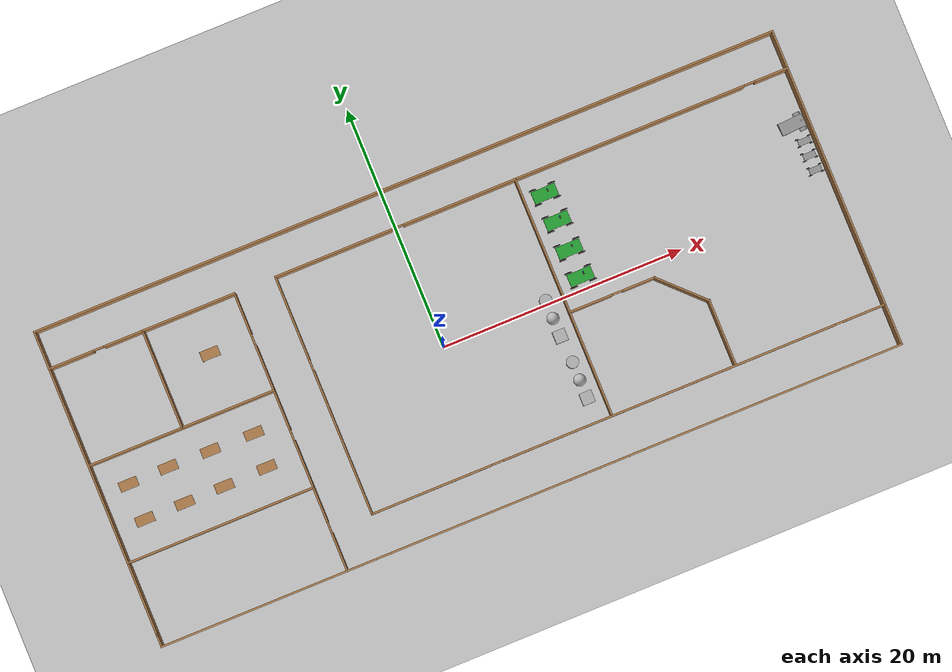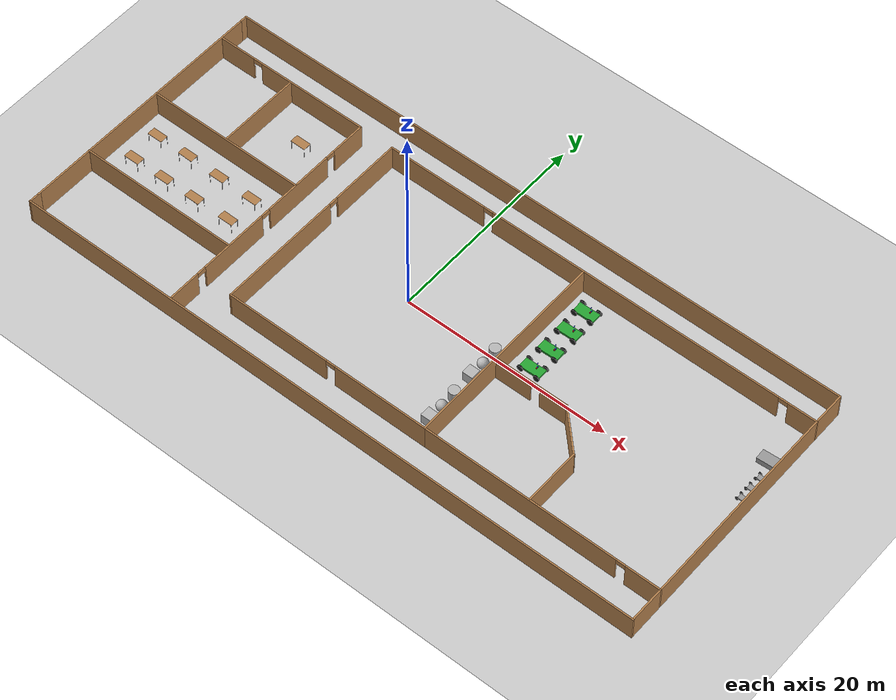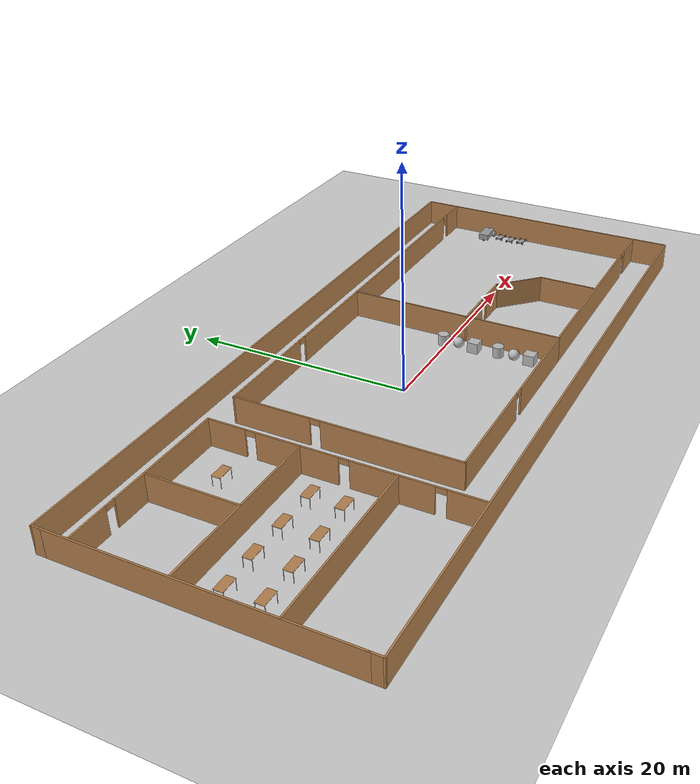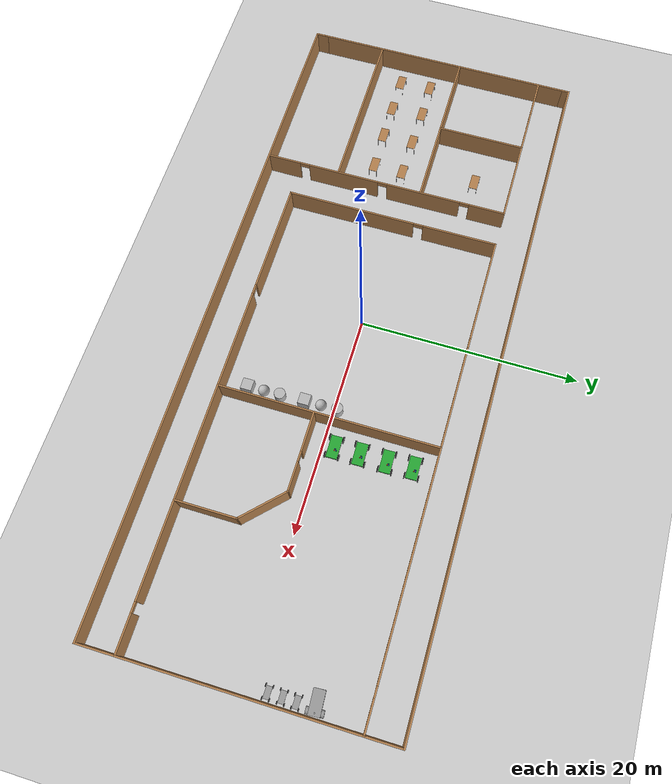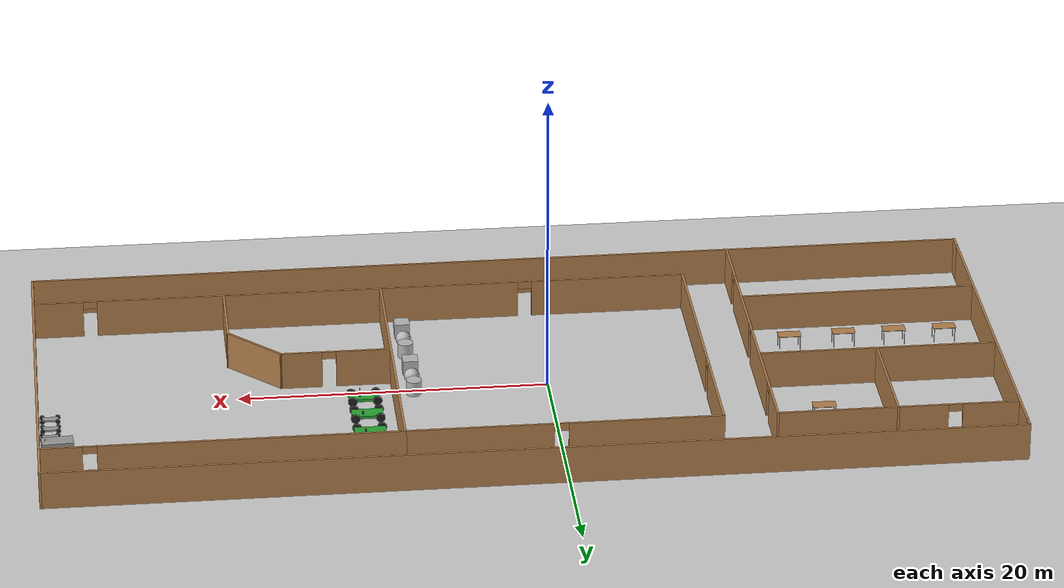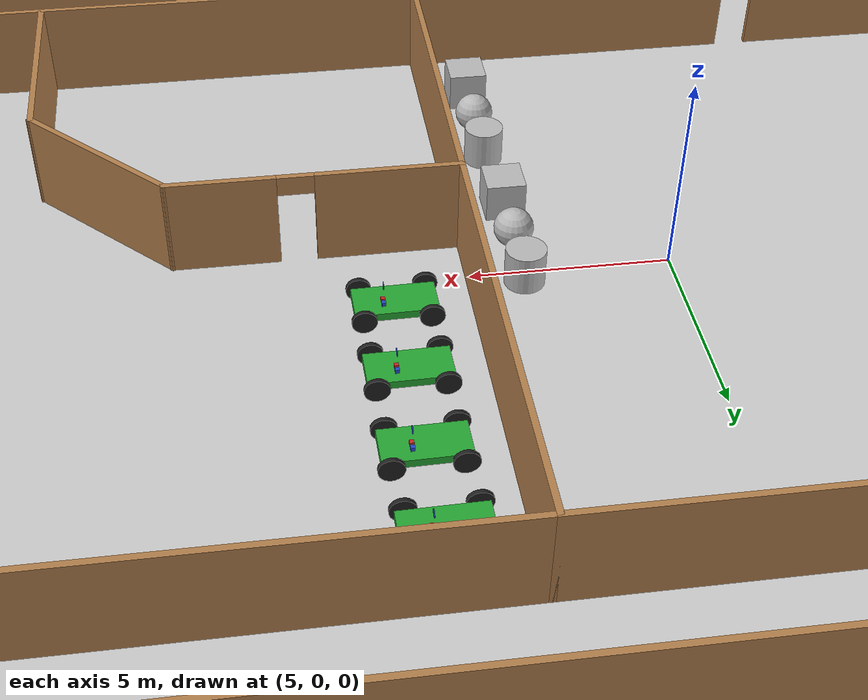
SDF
<sdf version="1.7">
 <world name="default">
  <light name="sun" type="directional">
   <pose>0 0 10 0 -0 0</pose>
   <diffuse>0.8 0.8 0.8 1</diffuse>
   <specular>0.2 0.2 0.2 1</specular>
   <attenuation>
    <range>1000</range>
    <constant>0.9</constant>
    <linear>0.01</linear>
    <quadratic>0.001</quadratic>
   </attenuation>
   <direction>-0.5 0.1 -0.9</direction>
   <spot><inner_angle>0</inner_angle><outer_angle>0</outer_angle><falloff>0</falloff></spot>
  </light>
  <model name="ground_plane">
   <static>1</static>
   <link name="link">
    <collision name="collision">
     <geometry><plane><normal>0 0 1</normal><size>100 100</size></plane></geometry>
     <surface>
      <contact><collide_bitmask>65535</collide_bitmask></contact>
      <friction><ode><mu>100</mu><mu2>50</mu2></ode></friction>
     </surface>
    </collision>
    <visual name="visual">
     <cast_shadows>0</cast_shadows>
     <geometry><plane><normal>0 0 1</normal><size>100 100</size></plane></geometry>
     <material>
      <script><uri>file://media/materials/scripts/gazebo.material</uri><name>Gazebo/Grey</name></script>
     </material>
    </visual>
   </link>
  </model>
  <gravity>0 0 -9.8</gravity>
  <magnetic_field>6e-06 2.3e-05 -4.2e-05</magnetic_field>
  <atmosphere type="adiabatic"/>
  <physics type="ode">
   <max_step_size>0.001</max_step_size>
   <real_time_factor>1</real_time_factor>
   <real_time_update_rate>1000</real_time_update_rate>
  </physics>
  <scene><ambient>0.4 0.4 0.4 1</ambient><background>0.7 0.7 0.7 1</background><shadows>1</shadows></scene>
  <audio><device>default</device></audio>
  <spherical_coordinates>
   <surface_model>EARTH_WGS84</surface_model>
   <latitude_deg>0</latitude_deg>
   <longitude_deg>0</longitude_deg>
   <elevation>0</elevation>
   <heading_deg>0</heading_deg>
  </spherical_coordinates>
  <model name="Industry_0">
   <pose>1.95149 -0.16782 0 0 -0 0</pose>
   <link name="Wall_107">
    <pose>-1.975 10.05 0 0 -0 0</pose>
    <visual name="Wall_107_Visual_0">
     <pose>-5.18531 0 1.25 0 -0 0</pose>
     <geometry><box><size>9.87937 0.15 2.5</size></box></geometry>
     <material>
      <script><uri>file://media/materials/scripts/gazebo.material</uri><name>Gazebo/Wood</name></script>
      <ambient>1 1 1 1</ambient>
     </material>
     <meta><layer>0</layer></meta>
    </visual>
    <collision name="Wall_107_Collision_0">
     <geometry><box><size>9.87937 0.15 2.5</size></box></geometry>
     <pose>-5.18531 0 1.25 0 -0 0</pose>
    </collision>
    <visual name="Wall_107_Visual_1">
     <pose>5.38969 0 1.25 0 -0 0</pose>
     <geometry><box><size>9.47063 0.15 2.5</size></box></geometry>
     <material>
      <script><uri>file://media/materials/scripts/gazebo.material</uri><name>Gazebo/Wood</name></script>
      <ambient>1 1 1 1</ambient>
     </material>
     <meta><layer>0</layer></meta>
    </visual>
    <collision name="Wall_107_Collision_1">
     <geometry><box><size>9.47063 0.15 2.5</size></box></geometry>
     <pose>5.38969 0 1.25 0 -0 0</pose>
    </collision>
    <visual name="Wall_107_Visual_2">
     <pose>0.204375 0 2.25 0 -0 0</pose>
     <geometry><box><size>0.9 0.15 0.5</size></box></geometry>
     <material>
      <script><uri>file://media/materials/scripts/gazebo.material</uri><name>Gazebo/Wood</name></script>
      <ambient>1 1 1 1</ambient>
     </material>
     <meta><layer>0</layer></meta>
    </visual>
    <collision name="Wall_107_Collision_2">
     <geometry><box><size>0.9 0.15 0.5</size></box></geometry>
     <pose>0.204375 0 2.25 0 -0 0</pose>
    </collision>
   </link>
   <link name="Wall_108">
    <collision name="Wall_108_Collision">
     <geometry><box><size>20 0.15 2.5</size></box></geometry>
     <pose>0 0 1.25 0 -0 0</pose>
    </collision>
    <visual name="Wall_108_Visual">
     <pose>0 0 1.25 0 -0 0</pose>
     <geometry><box><size>20 0.15 2.5</size></box></geometry>
     <material>
      <script><uri>file://media/materials/scripts/gazebo.material</uri><name>Gazebo/Wood</name></script>
      <ambient>1 1 1 1</ambient>
     </material>
     <meta><layer>0</layer></meta>
    </visual>
    <pose>8.075 0.125 0 0 -0 -1.5708</pose>
   </link>
   <link name="Wall_109">
    <pose>-1.975 -9.8 0 0 -0 3.14159</pose>
    <visual name="Wall_109_Visual_0">
     <pose>-5.52872 0 1.25 0 -0 0</pose>
     <geometry><box><size>9.19257 0.15 2.5</size></box></geometry>
     <material>
      <script><uri>file://media/materials/scripts/gazebo.material</uri><name>Gazebo/Wood</name></script>
      <ambient>1 1 1 1</ambient>
     </material>
     <meta><layer>0</layer></meta>
    </visual>
    <collision name="Wall_109_Collision_0">
     <geometry><box><size>9.19257 0.15 2.5</size></box></geometry>
     <pose>-5.52872 0 1.25 0 -0 0</pose>
    </collision>
    <visual name="Wall_109_Visual_1">
     <pose>5.04629 0 1.25 0 -0 0</pose>
     <geometry><box><size>10.1574 0.15 2.5</size></box></geometry>
     <material>
      <script><uri>file://media/materials/scripts/gazebo.material</uri><name>Gazebo/Wood</name></script>
      <ambient>1 1 1 1</ambient>
     </material>
     <meta><layer>0</layer></meta>
    </visual>
    <collision name="Wall_109_Collision_1">
     <geometry><box><size>10.1574 0.15 2.5</size></box></geometry>
     <pose>5.04629 0 1.25 0 -0 0</pose>
    </collision>
    <visual name="Wall_109_Visual_2">
     <pose>-0.482429 0 2.25 0 -0 0</pose>
     <geometry><box><size>0.9 0.15 0.5</size></box></geometry>
     <material>
      <script><uri>file://media/materials/scripts/gazebo.material</uri><name>Gazebo/Wood</name></script>
      <ambient>1 1 1 1</ambient>
     </material>
     <meta><layer>0</layer></meta>
    </visual>
    <collision name="Wall_109_Collision_2">
     <geometry><box><size>0.9 0.15 0.5</size></box></geometry>
     <pose>-0.482429 0 2.25 0 -0 0</pose>
    </collision>
   </link>
   <link name="Wall_111">
    <pose>-12.025 0.125 0 0 -0 -1.5708</pose>
    <visual name="Wall_111_Visual_0">
     <pose>-6.49758 0 1.25 0 -0 0</pose>
     <geometry><box><size>7.00483 0.15 2.5</size></box></geometry>
     <material>
      <script><uri>file://media/materials/scripts/gazebo.material</uri><name>Gazebo/Wood</name></script>
      <ambient>1 1 1 1</ambient>
     </material>
     <meta><layer>0</layer></meta>
    </visual>
    <collision name="Wall_111_Collision_0">
     <geometry><box><size>7.00483 0.15 2.5</size></box></geometry>
     <pose>-6.49758 0 1.25 0 -0 0</pose>
    </collision>
    <visual name="Wall_111_Visual_1">
     <pose>3.95241 0 1.25 0 -0 0</pose>
     <geometry><box><size>12.0952 0.15 2.5</size></box></geometry>
     <material>
      <script><uri>file://media/materials/scripts/gazebo.material</uri><name>Gazebo/Wood</name></script>
      <ambient>1 1 1 1</ambient>
     </material>
     <meta><layer>0</layer></meta>
    </visual>
    <collision name="Wall_111_Collision_1">
     <geometry><box><size>12.0952 0.15 2.5</size></box></geometry>
     <pose>3.95241 0 1.25 0 -0 0</pose>
    </collision>
    <visual name="Wall_111_Visual_2">
     <pose>-2.54517 0 2.25 0 -0 0</pose>
     <geometry><box><size>0.9 0.15 0.5</size></box></geometry>
     <material>
      <script><uri>file://media/materials/scripts/gazebo.material</uri><name>Gazebo/Wood</name></script>
      <ambient>1 1 1 1</ambient>
     </material>
     <meta><layer>0</layer></meta>
    </visual>
    <collision name="Wall_111_Collision_2">
     <geometry><box><size>0.9 0.15 0.5</size></box></geometry>
     <pose>-2.54517 0 2.25 0 -0 0</pose>
    </collision>
   </link>
   <link name="Wall_113">
    <pose>19.5 10.05 0 0 -0 0</pose>
    <visual name="Wall_113_Visual_0">
     <pose>-1.84564 0 1.25 0 -0 0</pose>
     <geometry><box><size>19.3087 0.15 2.5</size></box></geometry>
     <material>
      <script><uri>file://media/materials/scripts/gazebo.material</uri><name>Gazebo/Wood</name></script>
      <ambient>1 1 1 1</ambient>
     </material>
     <meta><layer>0</layer></meta>
    </visual>
    <collision name="Wall_113_Collision_0">
     <geometry><box><size>19.3087 0.15 2.5</size></box></geometry>
     <pose>-1.84564 0 1.25 0 -0 0</pose>
    </collision>
    <visual name="Wall_113_Visual_1">
     <pose>10.1044 0 1.25 0 -0 0</pose>
     <geometry><box><size>2.79128 0.15 2.5</size></box></geometry>
     <material>
      <script><uri>file://media/materials/scripts/gazebo.material</uri><name>Gazebo/Wood</name></script>
      <ambient>1 1 1 1</ambient>
     </material>
     <meta><layer>0</layer></meta>
    </visual>
    <collision name="Wall_113_Collision_1">
     <geometry><box><size>2.79128 0.15 2.5</size></box></geometry>
     <pose>10.1044 0 1.25 0 -0 0</pose>
    </collision>
    <visual name="Wall_113_Visual_2">
     <pose>8.25872 0 2.25 0 -0 0</pose>
     <geometry><box><size>0.9 0.15 0.5</size></box></geometry>
     <material>
      <script><uri>file://media/materials/scripts/gazebo.material</uri><name>Gazebo/Wood</name></script>
      <ambient>1 1 1 1</ambient>
     </material>
     <meta><layer>0</layer></meta>
    </visual>
    <collision name="Wall_113_Collision_2">
     <geometry><box><size>0.9 0.15 0.5</size></box></geometry>
     <pose>8.25872 0 2.25 0 -0 0</pose>
    </collision>
   </link>
   <link name="Wall_114">
    <collision name="Wall_114_Collision">
     <geometry><box><size>20 0.15 2.5</size></box></geometry>
     <pose>0 0 1.25 0 -0 0</pose>
    </collision>
    <visual name="Wall_114_Visual">
     <pose>0 0 1.25 0 -0 0</pose>
     <geometry><box><size>20 0.15 2.5</size></box></geometry>
     <material>
      <script><uri>file://media/materials/scripts/gazebo.material</uri><name>Gazebo/Wood</name></script>
      <ambient>1 1 1 1</ambient>
     </material>
     <meta><layer>0</layer></meta>
    </visual>
    <pose>30.925 0.125 0 0 -0 -1.5708</pose>
   </link>
   <link name="Wall_115">
    <pose>19.5 -9.8 0 0 -0 3.14159</pose>
    <visual name="Wall_115_Visual_0">
     <pose>-9.82631 0 1.25 0 -0 0</pose>
     <geometry><box><size>3.34739 0.15 2.5</size></box></geometry>
     <material>
      <script><uri>file://media/materials/scripts/gazebo.material</uri><name>Gazebo/Wood</name></script>
      <ambient>1 1 1 1</ambient>
     </material>
     <meta><layer>0</layer></meta>
    </visual>
    <collision name="Wall_115_Collision_0">
     <geometry><box><size>3.34739 0.15 2.5</size></box></geometry>
     <pose>-9.82631 0 1.25 0 -0 0</pose>
    </collision>
    <visual name="Wall_115_Visual_1">
     <pose>2.12369 0 1.25 0 -0 0</pose>
     <geometry><box><size>18.7526 0.15 2.5</size></box></geometry>
     <material>
      <script><uri>file://media/materials/scripts/gazebo.material</uri><name>Gazebo/Wood</name></script>
      <ambient>1 1 1 1</ambient>
     </material>
     <meta><layer>0</layer></meta>
    </visual>
    <collision name="Wall_115_Collision_1">
     <geometry><box><size>18.7526 0.15 2.5</size></box></geometry>
     <pose>2.12369 0 1.25 0 -0 0</pose>
    </collision>
    <visual name="Wall_115_Visual_2">
     <pose>-7.70261 0 2.25 0 -0 0</pose>
     <geometry><box><size>0.9 0.15 0.5</size></box></geometry>
     <material>
      <script><uri>file://media/materials/scripts/gazebo.material</uri><name>Gazebo/Wood</name></script>
      <ambient>1 1 1 1</ambient>
     </material>
     <meta><layer>0</layer></meta>
    </visual>
    <collision name="Wall_115_Collision_2">
     <geometry><box><size>0.9 0.15 0.5</size></box></geometry>
     <pose>-7.70261 0 2.25 0 -0 0</pose>
    </collision>
   </link>
   <link name="Wall_119">
    <collision name="Wall_119_Collision">
     <geometry><box><size>24.75 0.15 2.5</size></box></geometry>
     <pose>0 0 1.25 0 -0 0</pose>
    </collision>
    <visual name="Wall_119_Visual">
     <pose>0 0 1.25 0 -0 0</pose>
     <geometry><box><size>24.75 0.15 2.5</size></box></geometry>
     <material>
      <script><uri>file://media/materials/scripts/gazebo.material</uri><name>Gazebo/Wood</name></script>
      <ambient>1 1 1 1</ambient>
     </material>
     <meta><layer>0</layer></meta>
    </visual>
    <pose>-30.925 0.1 0 0 -0 -1.5708</pose>
   </link>
   <link name="Wall_135">
    <collision name="Wall_135_Collision">
     <geometry><box><size>3.25 0.15 2.5</size></box></geometry>
     <pose>0 0 1.25 0 -0 0</pose>
    </collision>
    <visual name="Wall_135_Visual">
     <pose>0 0 1.25 0 -0 0</pose>
     <geometry><box><size>3.25 0.15 2.5</size></box></geometry>
     <material>
      <script><uri>file://media/materials/scripts/gazebo.material</uri><name>Gazebo/Wood</name></script>
      <ambient>1 1 1 1</ambient>
     </material>
     <meta><layer>0</layer></meta>
    </visual>
    <pose>30.925 11.6 0 0 -0 1.5708</pose>
   </link>
   <link name="Wall_136">
    <collision name="Wall_136_Collision">
     <geometry><box><size>62 0.15 2.5</size></box></geometry>
     <pose>0 0 1.25 0 -0 0</pose>
    </collision>
    <visual name="Wall_136_Visual">
     <pose>0 0 1.25 0 -0 0</pose>
     <geometry><box><size>62 0.15 2.5</size></box></geometry>
     <material>
      <script><uri>file://media/materials/scripts/gazebo.material</uri><name>Gazebo/Wood</name></script>
      <ambient>1 1 1 1</ambient>
     </material>
     <meta><layer>0</layer></meta>
    </visual>
    <pose>1e-06 13.15 0 0 -0 3.14159</pose>
   </link>
   <link name="Wall_137">
    <collision name="Wall_137_Collision">
     <geometry><box><size>0.9 0.15 2.5</size></box></geometry>
     <pose>0 0 1.25 0 -0 0</pose>
    </collision>
    <visual name="Wall_137_Visual">
     <pose>0 0 1.25 0 -0 0</pose>
     <geometry><box><size>0.9 0.15 2.5</size></box></geometry>
     <material>
      <script><uri>file://media/materials/scripts/gazebo.material</uri><name>Gazebo/Wood</name></script>
      <ambient>1 1 1 1</ambient>
     </material>
     <meta><layer>0</layer></meta>
    </visual>
    <pose>-30.925 12.775 0 0 -0 -1.5708</pose>
   </link>
   <link name="Wall_139">
    <collision name="Wall_139_Collision">
     <geometry><box><size>3.5 0.15 2.5</size></box></geometry>
     <pose>0 0 1.25 0 -0 0</pose>
    </collision>
    <visual name="Wall_139_Visual">
     <pose>0 0 1.25 0 -0 0</pose>
     <geometry><box><size>3.5 0.15 2.5</size></box></geometry>
     <material>
      <script><uri>file://media/materials/scripts/gazebo.material</uri><name>Gazebo/Wood</name></script>
      <ambient>1 1 1 1</ambient>
     </material>
     <meta><layer>0</layer></meta>
    </visual>
    <pose>30.925 -11.475 0 0 -0 -1.5708</pose>
   </link>
   <link name="Wall_140">
    <collision name="Wall_140_Collision">
     <geometry><box><size>62 0.15 2.5</size></box></geometry>
     <pose>0 0 1.25 0 -0 0</pose>
    </collision>
    <visual name="Wall_140_Visual">
     <pose>0 0 1.25 0 -0 0</pose>
     <geometry><box><size>62 0.15 2.5</size></box></geometry>
     <material>
      <script><uri>file://media/materials/scripts/gazebo.material</uri><name>Gazebo/Wood</name></script>
      <ambient>1 1 1 1</ambient>
     </material>
     <meta><layer>0</layer></meta>
    </visual>
    <pose>1e-06 -13.15 0 0 -0 3.14159</pose>
   </link>
   <link name="Wall_141">
    <collision name="Wall_141_Collision">
     <geometry><box><size>1.25 0.15 2.5</size></box></geometry>
     <pose>0 0 1.25 0 -0 0</pose>
    </collision>
    <visual name="Wall_141_Visual">
     <pose>0 0 1.25 0 -0 0</pose>
     <geometry><box><size>1.25 0.15 2.5</size></box></geometry>
     <material>
      <script><uri>file://media/materials/scripts/gazebo.material</uri><name>Gazebo/Wood</name></script>
      <ambient>1 1 1 1</ambient>
     </material>
     <meta><layer>0</layer></meta>
    </visual>
    <pose>-30.925 -12.6 0 0 -0 1.5708</pose>
   </link>
   <link name="Wall_150">
    <pose>-15.4509 -1.48359 0 0 -0 -1.5708</pose>
    <visual name="Wall_150_Visual_0">
     <pose>-9.89393 0 1.25 0 -0 0</pose>
     <geometry><box><size>3.46215 0.15 2.5</size></box></geometry>
     <material>
      <script><uri>file://media/materials/scripts/gazebo.material</uri><name>Gazebo/Wood</name></script>
      <ambient>1 1 1 1</ambient>
     </material>
     <meta><layer>0</layer></meta>
    </visual>
    <collision name="Wall_150_Collision_0">
     <geometry><box><size>3.46215 0.15 2.5</size></box></geometry>
     <pose>-9.89393 0 1.25 0 -0 0</pose>
    </collision>
    <visual name="Wall_150_Visual_1">
     <pose>-3.70887 0 1.25 0 -0 0</pose>
     <geometry><box><size>7.10796 0.15 2.5</size></box></geometry>
     <material>
      <script><uri>file://media/materials/scripts/gazebo.material</uri><name>Gazebo/Wood</name></script>
      <ambient>1 1 1 1</ambient>
     </material>
     <meta><layer>0</layer></meta>
    </visual>
    <collision name="Wall_150_Collision_1">
     <geometry><box><size>7.10796 0.15 2.5</size></box></geometry>
     <pose>-3.70887 0 1.25 0 -0 0</pose>
    </collision>
    <visual name="Wall_150_Visual_2">
     <pose>4.16006 0 1.25 0 -0 0</pose>
     <geometry><box><size>6.8299 0.15 2.5</size></box></geometry>
     <material>
      <script><uri>file://media/materials/scripts/gazebo.material</uri><name>Gazebo/Wood</name></script>
      <ambient>1 1 1 1</ambient>
     </material>
     <meta><layer>0</layer></meta>
    </visual>
    <collision name="Wall_150_Collision_2">
     <geometry><box><size>6.8299 0.15 2.5</size></box></geometry>
     <pose>4.16006 0 1.25 0 -0 0</pose>
    </collision>
    <visual name="Wall_150_Visual_3">
     <pose>10.05 0 1.25 0 -0 0</pose>
     <geometry><box><size>3.14999 0.15 2.5</size></box></geometry>
     <material>
      <script><uri>file://media/materials/scripts/gazebo.material</uri><name>Gazebo/Wood</name></script>
      <ambient>1 1 1 1</ambient>
     </material>
     <meta><layer>0</layer></meta>
    </visual>
    <collision name="Wall_150_Collision_3">
     <geometry><box><size>3.14999 0.15 2.5</size></box></geometry>
     <pose>10.05 0 1.25 0 -0 0</pose>
    </collision>
    <visual name="Wall_150_Visual_4">
     <pose>-7.71285 0 2.25 0 -0 0</pose>
     <geometry><box><size>0.9 0.15 0.5</size></box></geometry>
     <material>
      <script><uri>file://media/materials/scripts/gazebo.material</uri><name>Gazebo/Wood</name></script>
      <ambient>1 1 1 1</ambient>
     </material>
     <meta><layer>0</layer></meta>
    </visual>
    <collision name="Wall_150_Collision_4">
     <geometry><box><size>0.9 0.15 0.5</size></box></geometry>
     <pose>-7.71285 0 2.25 0 -0 0</pose>
    </collision>
    <visual name="Wall_150_Visual_5">
     <pose>0.295105 0 2.25 0 -0 0</pose>
     <geometry><box><size>0.9 0.15 0.5</size></box></geometry>
     <material>
      <script><uri>file://media/materials/scripts/gazebo.material</uri><name>Gazebo/Wood</name></script>
      <ambient>1 1 1 1</ambient>
     </material>
     <meta><layer>0</layer></meta>
    </visual>
    <collision name="Wall_150_Collision_5">
     <geometry><box><size>0.9 0.15 0.5</size></box></geometry>
     <pose>0.295105 0 2.25 0 -0 0</pose>
    </collision>
    <visual name="Wall_150_Visual_6">
     <pose>8.02501 0 2.25 0 -0 0</pose>
     <geometry><box><size>0.9 0.15 0.5</size></box></geometry>
     <material>
      <script><uri>file://media/materials/scripts/gazebo.material</uri><name>Gazebo/Wood</name></script>
      <ambient>1 1 1 1</ambient>
     </material>
     <meta><layer>0</layer></meta>
    </visual>
    <collision name="Wall_150_Collision_6">
     <geometry><box><size>0.9 0.15 0.5</size></box></geometry>
     <pose>8.02501 0 2.25 0 -0 0</pose>
    </collision>
   </link>
   <link name="Wall_152">
    <pose>-23.1259 10.0664 0 0 -0 3.14159</pose>
    <visual name="Wall_152_Visual_0">
     <pose>-2.2652 0 1.25 0 -0 0</pose>
     <geometry><box><size>10.9696 0.15 2.5</size></box></geometry>
     <material>
      <script><uri>file://media/materials/scripts/gazebo.material</uri><name>Gazebo/Wood</name></script>
      <ambient>1 1 1 1</ambient>
     </material>
     <meta><layer>0</layer></meta>
    </visual>
    <collision name="Wall_152_Collision_0">
     <geometry><box><size>10.9696 0.15 2.5</size></box></geometry>
     <pose>-2.2652 0 1.25 0 -0 0</pose>
    </collision>
    <visual name="Wall_152_Visual_1">
     <pose>5.9348 0 1.25 0 -0 0</pose>
     <geometry><box><size>3.63039 0.15 2.5</size></box></geometry>
     <material>
      <script><uri>file://media/materials/scripts/gazebo.material</uri><name>Gazebo/Wood</name></script>
      <ambient>1 1 1 1</ambient>
     </material>
     <meta><layer>0</layer></meta>
    </visual>
    <collision name="Wall_152_Collision_1">
     <geometry><box><size>3.63039 0.15 2.5</size></box></geometry>
     <pose>5.9348 0 1.25 0 -0 0</pose>
    </collision>
    <visual name="Wall_152_Visual_2">
     <pose>3.66961 0 2.25 0 -0 0</pose>
     <geometry><box><size>0.9 0.15 0.5</size></box></geometry>
     <material>
      <script><uri>file://media/materials/scripts/gazebo.material</uri><name>Gazebo/Wood</name></script>
      <ambient>1 1 1 1</ambient>
     </material>
     <meta><layer>0</layer></meta>
    </visual>
    <collision name="Wall_152_Collision_2">
     <geometry><box><size>0.9 0.15 0.5</size></box></geometry>
     <pose>3.66961 0 2.25 0 -0 0</pose>
    </collision>
   </link>
   <link name="Wall_156">
    <collision name="Wall_156_Collision">
     <geometry><box><size>15.5 0.15 2.5</size></box></geometry>
     <pose>0 0 1.25 0 -0 0</pose>
    </collision>
    <visual name="Wall_156_Visual">
     <pose>0 0 1.25 0 -0 0</pose>
     <geometry><box><size>15.5 0.15 2.5</size></box></geometry>
     <material>
      <script><uri>file://media/materials/scripts/gazebo.material</uri><name>Gazebo/Wood</name></script>
      <ambient>1 1 1 1</ambient>
     </material>
     <meta><layer>0</layer></meta>
    </visual>
    <pose>-23.2371 -6.17195 0 0 -0 3.14159</pose>
   </link>
   <link name="Wall_158">
    <collision name="Wall_158_Collision">
     <geometry><box><size>15.5 0.15 2.5</size></box></geometry>
     <pose>0 0 1.25 0 -0 0</pose>
    </collision>
    <visual name="Wall_158_Visual">
     <pose>0 0 1.25 0 -0 0</pose>
     <geometry><box><size>15.5 0.15 2.5</size></box></geometry>
     <material>
      <script><uri>file://media/materials/scripts/gazebo.material</uri><name>Gazebo/Wood</name></script>
      <ambient>1 1 1 1</ambient>
     </material>
     <meta><layer>0</layer></meta>
    </visual>
    <pose>-23.1815 1.94723 0 0 -0 3.14159</pose>
   </link>
   <link name="Wall_162">
    <collision name="Wall_162_Collision">
     <geometry><box><size>8.25 0.15 2.5</size></box></geometry>
     <pose>0 0 1.25 0 -0 0</pose>
    </collision>
    <visual name="Wall_162_Visual">
     <pose>0 0 1.25 0 -0 0</pose>
     <geometry><box><size>8.25 0.15 2.5</size></box></geometry>
     <material>
      <script><uri>file://media/materials/scripts/gazebo.material</uri><name>Gazebo/Wood</name></script>
      <ambient>1 1 1 1</ambient>
     </material>
     <meta><layer>0</layer></meta>
    </visual>
    <pose>-23.1252 6.01641 0 0 -0 -1.5708</pose>
   </link>
   <link name="Wall_166">
    <pose>11.6225 -1.11137 0 0 -0 0</pose>
    <visual name="Wall_166_Visual_0">
     <pose>-1.81051 0 1.25 0 -0 0</pose>
     <geometry><box><size>3.62898 0.15 2.5</size></box></geometry>
     <material>
      <script><uri>file://media/materials/scripts/gazebo.material</uri><name>Gazebo/Wood</name></script>
      <ambient>1 1 1 1</ambient>
     </material>
     <meta><layer>0</layer></meta>
    </visual>
    <collision name="Wall_166_Collision_0">
     <geometry><box><size>3.62898 0.15 2.5</size></box></geometry>
     <pose>-1.81051 0 1.25 0 -0 0</pose>
    </collision>
    <visual name="Wall_166_Visual_1">
     <pose>2.26449 0 1.25 0 -0 0</pose>
     <geometry><box><size>2.72102 0.15 2.5</size></box></geometry>
     <material>
      <script><uri>file://media/materials/scripts/gazebo.material</uri><name>Gazebo/Wood</name></script>
      <ambient>1 1 1 1</ambient>
     </material>
     <meta><layer>0</layer></meta>
    </visual>
    <collision name="Wall_166_Collision_1">
     <geometry><box><size>2.72102 0.15 2.5</size></box></geometry>
     <pose>2.26449 0 1.25 0 -0 0</pose>
    </collision>
    <visual name="Wall_166_Visual_2">
     <pose>0.453979 0 2.25 0 -0 0</pose>
     <geometry><box><size>0.9 0.15 0.5</size></box></geometry>
     <material>
      <script><uri>file://media/materials/scripts/gazebo.material</uri><name>Gazebo/Wood</name></script>
      <ambient>1 1 1 1</ambient>
     </material>
     <meta><layer>0</layer></meta>
    </visual>
    <collision name="Wall_166_Collision_2">
     <geometry><box><size>0.9 0.15 0.5</size></box></geometry>
     <pose>0.453979 0 2.25 0 -0 0</pose>
    </collision>
   </link>
   <link name="Wall_167">
    <collision name="Wall_167_Collision">
     <geometry><box><size>4.75 0.15 2.5</size></box></geometry>
     <pose>0 0 1.25 0 -0 0</pose>
    </collision>
    <visual name="Wall_167_Visual">
     <pose>0 0 1.25 0 -0 0</pose>
     <geometry><box><size>4.75 0.15 2.5</size></box></geometry>
     <material>
      <script><uri>file://media/materials/scripts/gazebo.material</uri><name>Gazebo/Wood</name></script>
      <ambient>1 1 1 1</ambient>
     </material>
     <meta><layer>0</layer></meta>
    </visual>
    <pose>16.7988 -2.73771 0 0 -0 -0.785398</pose>
   </link>
   <link name="Wall_168">
    <collision name="Wall_168_Collision">
     <geometry><box><size>5.5 0.15 2.5</size></box></geometry>
     <pose>0 0 1.25 0 -0 0</pose>
    </collision>
    <visual name="Wall_168_Visual">
     <pose>0 0 1.25 0 -0 0</pose>
     <geometry><box><size>5.5 0.15 2.5</size></box></geometry>
     <material>
      <script><uri>file://media/materials/scripts/gazebo.material</uri><name>Gazebo/Wood</name></script>
      <ambient>1 1 1 1</ambient>
     </material>
     <meta><layer>0</layer></meta>
    </visual>
    <pose>18.4252 -7.03906 0 0 -0 -1.5708</pose>
   </link>
   <static>1</static>
  </model>
  <model name="table">
   <static>1</static>
   <link name="link">
    <collision name="surface">
     <pose>0 0 1 0 -0 0</pose>
     <geometry><box><size>1.5 0.8 0.03</size></box></geometry>
     <surface><friction><ode><mu>0.6</mu><mu2>0.6</mu2></ode></friction></surface>
    </collision>
    <visual name="visual1">
     <pose>0 0 1 0 -0 0</pose>
     <geometry><box><size>1.5 0.8 0.03</size></box></geometry>
     <material>
      <script><uri>file://media/materials/scripts/gazebo.material</uri><name>Gazebo/Wood</name></script>
     </material>
    </visual>
    <collision name="front_left_leg">
     <pose>0.68 0.38 0.5 0 -0 0</pose>
     <geometry><cylinder><radius>0.02</radius><length>1</length></cylinder></geometry>
    </collision>
    <visual name="front_left_leg">
     <pose>0.68 0.38 0.5 0 -0 0</pose>
     <geometry><cylinder><radius>0.02</radius><length>1</length></cylinder></geometry>
     <material>
      <script><uri>file://media/materials/scripts/gazebo.material</uri><name>Gazebo/Grey</name></script>
     </material>
    </visual>
    <collision name="front_right_leg">
     <pose>0.68 -0.38 0.5 0 -0 0</pose>
     <geometry><cylinder><radius>0.02</radius><length>1</length></cylinder></geometry>
    </collision>
    <visual name="front_right_leg">
     <pose>0.68 -0.38 0.5 0 -0 0</pose>
     <geometry><cylinder><radius>0.02</radius><length>1</length></cylinder></geometry>
     <material>
      <script><uri>file://media/materials/scripts/gazebo.material</uri><name>Gazebo/Grey</name></script>
     </material>
    </visual>
    <collision name="back_right_leg">
     <pose>-0.68 -0.38 0.5 0 -0 0</pose>
     <geometry><cylinder><radius>0.02</radius><length>1</length></cylinder></geometry>
    </collision>
    <visual name="back_right_leg">
     <pose>-0.68 -0.38 0.5 0 -0 0</pose>
     <geometry><cylinder><radius>0.02</radius><length>1</length></cylinder></geometry>
     <material>
      <script><uri>file://media/materials/scripts/gazebo.material</uri><name>Gazebo/Grey</name></script>
     </material>
    </visual>
    <collision name="back_left_leg">
     <pose>-0.68 0.38 0.5 0 -0 0</pose>
     <geometry><cylinder><radius>0.02</radius><length>1</length></cylinder></geometry>
    </collision>
    <visual name="back_left_leg">
     <pose>-0.68 0.38 0.5 0 -0 0</pose>
     <geometry><cylinder><radius>0.02</radius><length>1</length></cylinder></geometry>
     <material>
      <script><uri>file://media/materials/scripts/gazebo.material</uri><name>Gazebo/Grey</name></script>
     </material>
    </visual>
   </link>
   <pose>-17.05 6.36138 0 0 -0 0</pose>
  </model>
  <model name="textured_shapes">
   <pose>8.80989 -6.41031 0.51 0 -0 0</pose>
   <link name="box">
    <pose>0 -1.5 0 0 -0 0</pose>
    <collision name="collision"><geometry><box><size>1 1 1</size></box></geometry></collision>
    <visual name="visual">
     <geometry><box><size>1 1 1</size></box></geometry>
     <material>
      <script>
       <uri>model://textured_shapes/materials/scripts</uri>
       <uri>model://textured_shapes/materials/textures</uri>
       <name>TexturedShape/Squares</name>
      </script>
     </material>
    </visual>
    <inertial>
     <inertia><ixx>1</ixx><ixy>0</ixy><ixz>0</ixz><iyy>1</iyy><iyz>0</iyz><izz>1</izz></inertia>
     <mass>1</mass>
    </inertial>
   </link>
   <link name="sphere">
    <collision name="collision"><geometry><sphere><radius>0.5</radius></sphere></geometry></collision>
    <visual name="visual">
     <geometry><sphere><radius>0.5</radius></sphere></geometry>
     <material>
      <script>
       <uri>model://textured_shapes/materials/scripts</uri>
       <uri>model://textured_shapes/materials/textures</uri>
       <name>TexturedShape/Squares</name>
      </script>
     </material>
    </visual>
    <inertial>
     <inertia><ixx>1</ixx><ixy>0</ixy><ixz>0</ixz><iyy>1</iyy><iyz>0</iyz><izz>1</izz></inertia>
     <mass>1</mass>
    </inertial>
   </link>
   <link name="cylinder">
    <pose>0 1.5 0 0 -0 0</pose>
    <collision name="collision">
     <geometry><cylinder><radius>0.5</radius><length>1</length></cylinder></geometry>
    </collision>
    <visual name="visual">
     <geometry><cylinder><radius>0.5</radius><length>1</length></cylinder></geometry>
     <material>
      <script>
       <uri>model://textured_shapes/materials/scripts</uri>
       <uri>model://textured_shapes/materials/textures</uri>
       <name>TexturedShape/Squares</name>
      </script>
     </material>
    </visual>
    <inertial>
     <inertia><ixx>1</ixx><ixy>0</ixy><ixz>0</ixz><iyy>1</iyy><iyz>0</iyz><izz>1</izz></inertia>
     <mass>1</mass>
    </inertial>
   </link>
  </model>
  <model name="textured_shapes_0">
   <pose>8.6966 -1.17541 0.51 0 -0 0</pose>
   <link name="box">
    <pose>0 -1.5 0 0 -0 0</pose>
    <collision name="collision"><geometry><box><size>1 1 1</size></box></geometry></collision>
    <visual name="visual">
     <geometry><box><size>1 1 1</size></box></geometry>
     <material>
      <script>
       <uri>model://textured_shapes/materials/scripts</uri>
       <uri>model://textured_shapes/materials/textures</uri>
       <name>TexturedShape/Squares</name>
      </script>
     </material>
    </visual>
    <inertial>
     <inertia><ixx>1</ixx><ixy>0</ixy><ixz>0</ixz><iyy>1</iyy><iyz>0</iyz><izz>1</izz></inertia>
     <mass>1</mass>
    </inertial>
   </link>
   <link name="sphere">
    <collision name="collision"><geometry><sphere><radius>0.5</radius></sphere></geometry></collision>
    <visual name="visual">
     <geometry><sphere><radius>0.5</radius></sphere></geometry>
     <material>
      <script>
       <uri>model://textured_shapes/materials/scripts</uri>
       <uri>model://textured_shapes/materials/textures</uri>
       <name>TexturedShape/Squares</name>
      </script>
     </material>
    </visual>
    <inertial>
     <inertia><ixx>1</ixx><ixy>0</ixy><ixz>0</ixz><iyy>1</iyy><iyz>0</iyz><izz>1</izz></inertia>
     <mass>1</mass>
    </inertial>
   </link>
   <link name="cylinder">
    <pose>0 1.5 0 0 -0 0</pose>
    <collision name="collision">
     <geometry><cylinder><radius>0.5</radius><length>1</length></cylinder></geometry>
    </collision>
    <visual name="visual">
     <geometry><cylinder><radius>0.5</radius><length>1</length></cylinder></geometry>
     <material>
      <script>
       <uri>model://textured_shapes/materials/scripts</uri>
       <uri>model://textured_shapes/materials/textures</uri>
       <name>TexturedShape/Squares</name>
      </script>
     </material>
    </visual>
    <inertial>
     <inertia><ixx>1</ixx><ixy>0</ixy><ixz>0</ixz><iyy>1</iyy><iyz>0</iyz><izz>1</izz></inertia>
     <mass>1</mass>
    </inertial>
   </link>
  </model>
  <model name="car">
   <link name="chassis">
    <pose>0 0 0.3 0 -0 0</pose>
    <collision name="collision"><geometry><box><size>2 1 0.2</size></box></geometry></collision>
    <visual name="visual">
     <geometry><box><size>2 1 0.2</size></box></geometry>
     <material>
      <script><uri>file://media/materials/scripts/gazebo.material</uri><name>Gazebo/Green</name></script>
     </material>
    </visual>
    <inertial>
     <inertia><ixx>1</ixx><ixy>0</ixy><ixz>0</ixz><iyy>1</iyy><iyz>0</iyz><izz>1</izz></inertia>
     <mass>1</mass>
    </inertial>
   </link>
   <link name="front_left_wheel">
    <pose>0.8 0.6 0.3 -0 1.5707 1.5707</pose>
    <collision name="collision">
     <geometry><cylinder><radius>0.3</radius><length>0.1</length></cylinder></geometry>
    </collision>
    <visual name="visual">
     <geometry><cylinder><radius>0.3</radius><length>0.1</length></cylinder></geometry>
     <material>
      <script><uri>file://media/materials/scripts/gazebo.material</uri><name>Gazebo/Black</name></script>
     </material>
    </visual>
    <inertial>
     <inertia><ixx>1</ixx><ixy>0</ixy><ixz>0</ixz><iyy>1</iyy><iyz>0</iyz><izz>1</izz></inertia>
     <mass>1</mass>
    </inertial>
   </link>
   <link name="front_right_wheel">
    <pose>0.8 -0.6 0.3 -0 1.5707 1.5707</pose>
    <collision name="collision">
     <geometry><cylinder><radius>0.3</radius><length>0.1</length></cylinder></geometry>
    </collision>
    <visual name="visual">
     <geometry><cylinder><radius>0.3</radius><length>0.1</length></cylinder></geometry>
     <material>
      <script><uri>file://media/materials/scripts/gazebo.material</uri><name>Gazebo/Black</name></script>
     </material>
    </visual>
    <inertial>
     <inertia><ixx>1</ixx><ixy>0</ixy><ixz>0</ixz><iyy>1</iyy><iyz>0</iyz><izz>1</izz></inertia>
     <mass>1</mass>
    </inertial>
   </link>
   <link name="back_right_wheel">
    <pose>-0.8 -0.6 0.3 -0 1.5707 1.5707</pose>
    <collision name="collision">
     <geometry><cylinder><radius>0.3</radius><length>0.1</length></cylinder></geometry>
    </collision>
    <visual name="visual">
     <geometry><cylinder><radius>0.3</radius><length>0.1</length></cylinder></geometry>
     <material>
      <script><uri>file://media/materials/scripts/gazebo.material</uri><name>Gazebo/Black</name></script>
     </material>
    </visual>
    <inertial>
     <inertia><ixx>1</ixx><ixy>0</ixy><ixz>0</ixz><iyy>1</iyy><iyz>0</iyz><izz>1</izz></inertia>
     <mass>1</mass>
    </inertial>
   </link>
   <link name="back_left_wheel">
    <pose>-0.8 0.6 0.3 -0 1.5707 1.5707</pose>
    <collision name="collision">
     <geometry><cylinder><radius>0.3</radius><length>0.1</length></cylinder></geometry>
    </collision>
    <visual name="visual">
     <geometry><cylinder><radius>0.3</radius><length>0.1</length></cylinder></geometry>
     <material>
      <script><uri>file://media/materials/scripts/gazebo.material</uri><name>Gazebo/Black</name></script>
     </material>
    </visual>
    <inertial>
     <inertia><ixx>1</ixx><ixy>0</ixy><ixz>0</ixz><iyy>1</iyy><iyz>0</iyz><izz>1</izz></inertia>
     <mass>1</mass>
    </inertial>
   </link>
   <link name="gas_pedal">
    <pose>0.3 0.1 0.5 0 -0 0</pose>
    <collision name="collision"><geometry><box><size>0.1 0.1 0.1</size></box></geometry></collision>
    <visual name="visual">
     <geometry><box><size>0.1 0.1 0.1</size></box></geometry>
     <material>
      <script><uri>file://media/materials/scripts/gazebo.material</uri><name>Gazebo/Red</name></script>
     </material>
    </visual>
    <inertial>
     <inertia><ixx>1</ixx><ixy>0</ixy><ixz>0</ixz><iyy>1</iyy><iyz>0</iyz><izz>1</izz></inertia>
     <mass>1</mass>
    </inertial>
   </link>
   <link name="brake_pedal">
    <pose>0.3 0.25 0.5 0 -0 0</pose>
    <collision name="collision"><geometry><box><size>0.1 0.1 0.1</size></box></geometry></collision>
    <visual name="visual">
     <geometry><box><size>0.1 0.1 0.1</size></box></geometry>
     <material>
      <script><uri>file://media/materials/scripts/gazebo.material</uri><name>Gazebo/Blue</name></script>
     </material>
    </visual>
    <inertial>
     <inertia><ixx>1</ixx><ixy>0</ixy><ixz>0</ixz><iyy>1</iyy><iyz>0</iyz><izz>1</izz></inertia>
     <mass>1</mass>
    </inertial>
   </link>
   <link name="steering_wheel">
    <pose>0.3 0.2 1 0 1.5707 0</pose>
    <collision name="collision">
     <geometry><cylinder><radius>0.1</radius><length>0.01</length></cylinder></geometry>
    </collision>
    <visual name="visual">
     <geometry><cylinder><radius>0.1</radius><length>0.01</length></cylinder></geometry>
     <material>
      <script><uri>file://media/materials/scripts/gazebo.material</uri><name>Gazebo/Blue</name></script>
     </material>
    </visual>
    <inertial>
     <inertia><ixx>1</ixx><ixy>0</ixy><ixz>0</ixz><iyy>1</iyy><iyz>0</iyz><izz>1</izz></inertia>
     <mass>1</mass>
    </inertial>
   </link>
   <joint name="gas_joint" type="prismatic">
    <parent>chassis</parent>
    <child>gas_pedal</child>
    <axis>
     <xyz expressed_in="__model__">1 0 0</xyz>
     <limit><lower>0</lower><upper>0.2</upper></limit>
     <dynamics><spring_reference>0</spring_reference><spring_stiffness>0</spring_stiffness></dynamics>
    </axis>
   </joint>
   <joint name="brake_joint" type="prismatic">
    <parent>chassis</parent>
    <child>brake_pedal</child>
    <axis>
     <xyz expressed_in="__model__">1 0 0</xyz>
     <limit><lower>0</lower><upper>0.2</upper></limit>
     <dynamics><spring_reference>0</spring_reference><spring_stiffness>0</spring_stiffness></dynamics>
    </axis>
   </joint>
   <joint name="steering_joint" type="revolute">
    <parent>chassis</parent>
    <child>steering_wheel</child>
    <axis>
     <xyz expressed_in="__model__">1 0 0</xyz>
     <limit><lower>-7.853</lower><upper>7.853</upper></limit>
     <dynamics><spring_reference>0</spring_reference><spring_stiffness>0</spring_stiffness></dynamics>
    </axis>
   </joint>
   <joint name="front_left_joint" type="revolute2">
    <parent>chassis</parent>
    <child>front_left_wheel</child>
    <axis>
     <xyz expressed_in="__model__">0 0 1</xyz>
     <limit><lower>1.93258e-07</lower><upper>1.93258e-07</upper></limit>
     <dynamics><spring_reference>0</spring_reference><spring_stiffness>0</spring_stiffness></dynamics>
    </axis>
    <axis2>
     <xyz expressed_in="__model__">0 1 0</xyz>
     <limit><upper>1e+16</upper><lower>-1e+16</lower></limit>
     <dynamics><spring_reference>0</spring_reference><spring_stiffness>0</spring_stiffness></dynamics>
    </axis2>
    <physics><ode><limit><cfm>0</cfm><erp>0.9</erp></limit></ode></physics>
   </joint>
   <joint name="front_right_joint" type="revolute2">
    <parent>chassis</parent>
    <child>front_right_wheel</child>
    <axis>
     <xyz expressed_in="__model__">0 0 1</xyz>
     <limit><lower>1.93258e-07</lower><upper>1.93258e-07</upper></limit>
     <dynamics><spring_reference>0</spring_reference><spring_stiffness>0</spring_stiffness></dynamics>
    </axis>
    <axis2>
     <xyz expressed_in="__model__">0 1 0</xyz>
     <limit><upper>1e+16</upper><lower>-1e+16</lower></limit>
     <dynamics><spring_reference>0</spring_reference><spring_stiffness>0</spring_stiffness></dynamics>
    </axis2>
    <physics><ode><limit><cfm>0</cfm><erp>0.9</erp></limit></ode></physics>
   </joint>
   <joint name="back_right_joint" type="revolute2">
    <parent>chassis</parent>
    <child>back_right_wheel</child>
    <axis>
     <xyz expressed_in="__model__">0 0 1</xyz>
     <limit><lower>0</lower><upper>0</upper></limit>
     <dynamics><spring_reference>0</spring_reference><spring_stiffness>0</spring_stiffness></dynamics>
    </axis>
    <axis2>
     <xyz expressed_in="__model__">0 1 0</xyz>
     <limit><upper>1e+16</upper><lower>-1e+16</lower></limit>
     <dynamics><spring_reference>0</spring_reference><spring_stiffness>0</spring_stiffness></dynamics>
    </axis2>
    <physics><ode><limit><cfm>0</cfm><erp>0.9</erp></limit></ode></physics>
   </joint>
   <joint name="back_left_joint" type="revolute2">
    <parent>chassis</parent>
    <child>back_left_wheel</child>
    <axis>
     <xyz expressed_in="__model__">0 0 1</xyz>
     <limit><lower>0</lower><upper>0</upper></limit>
     <dynamics><spring_reference>0</spring_reference><spring_stiffness>0</spring_stiffness></dynamics>
    </axis>
    <axis2>
     <xyz expressed_in="__model__">0 1 0</xyz>
     <limit><upper>1e+16</upper><lower>-1e+16</lower></limit>
     <dynamics><spring_reference>0</spring_reference><spring_stiffness>0</spring_stiffness></dynamics>
    </axis2>
    <physics><ode><limit><cfm>0</cfm><erp>0.9</erp></limit></ode></physics>
   </joint>
   <plugin name="vehicle" filename="libVehiclePlugin.so">
    <front_left>front_left_joint</front_left>
    <front_right>front_right_joint</front_right>
    <back_left>back_left_joint</back_left>
    <back_right>back_right_joint</back_right>
    <gas>gas_joint</gas>
    <brake>brake_joint</brake>
    <steering>steering_joint</steering>
    <front_power>10</front_power>
    <rear_power>10</rear_power>
    <tire_angle_range>0.5</tire_angle_range>
    <max_speed>10</max_speed>
    <aero_load>0.1</aero_load>
   </plugin>
   <pose>11.8074 8.08034 0.010011 -7e-06 6e-06 0.014485</pose>
  </model>
  <model name="car_0">
   <link name="chassis">
    <pose>0 0 0.3 0 -0 0</pose>
    <collision name="collision"><geometry><box><size>2 1 0.2</size></box></geometry></collision>
    <visual name="visual">
     <geometry><box><size>2 1 0.2</size></box></geometry>
     <material>
      <script><uri>file://media/materials/scripts/gazebo.material</uri><name>Gazebo/Green</name></script>
     </material>
    </visual>
    <inertial>
     <inertia><ixx>1</ixx><ixy>0</ixy><ixz>0</ixz><iyy>1</iyy><iyz>0</iyz><izz>1</izz></inertia>
     <mass>1</mass>
    </inertial>
   </link>
   <link name="front_left_wheel">
    <pose>0.8 0.6 0.3 -0 1.5707 1.5707</pose>
    <collision name="collision">
     <geometry><cylinder><radius>0.3</radius><length>0.1</length></cylinder></geometry>
    </collision>
    <visual name="visual">
     <geometry><cylinder><radius>0.3</radius><length>0.1</length></cylinder></geometry>
     <material>
      <script><uri>file://media/materials/scripts/gazebo.material</uri><name>Gazebo/Black</name></script>
     </material>
    </visual>
    <inertial>
     <inertia><ixx>1</ixx><ixy>0</ixy><ixz>0</ixz><iyy>1</iyy><iyz>0</iyz><izz>1</izz></inertia>
     <mass>1</mass>
    </inertial>
   </link>
   <link name="front_right_wheel">
    <pose>0.8 -0.6 0.3 -0 1.5707 1.5707</pose>
    <collision name="collision">
     <geometry><cylinder><radius>0.3</radius><length>0.1</length></cylinder></geometry>
    </collision>
    <visual name="visual">
     <geometry><cylinder><radius>0.3</radius><length>0.1</length></cylinder></geometry>
     <material>
      <script><uri>file://media/materials/scripts/gazebo.material</uri><name>Gazebo/Black</name></script>
     </material>
    </visual>
    <inertial>
     <inertia><ixx>1</ixx><ixy>0</ixy><ixz>0</ixz><iyy>1</iyy><iyz>0</iyz><izz>1</izz></inertia>
     <mass>1</mass>
    </inertial>
   </link>
   <link name="back_right_wheel">
    <pose>-0.8 -0.6 0.3 -0 1.5707 1.5707</pose>
    <collision name="collision">
     <geometry><cylinder><radius>0.3</radius><length>0.1</length></cylinder></geometry>
    </collision>
    <visual name="visual">
     <geometry><cylinder><radius>0.3</radius><length>0.1</length></cylinder></geometry>
     <material>
      <script><uri>file://media/materials/scripts/gazebo.material</uri><name>Gazebo/Black</name></script>
     </material>
    </visual>
    <inertial>
     <inertia><ixx>1</ixx><ixy>0</ixy><ixz>0</ixz><iyy>1</iyy><iyz>0</iyz><izz>1</izz></inertia>
     <mass>1</mass>
    </inertial>
   </link>
   <link name="back_left_wheel">
    <pose>-0.8 0.6 0.3 -0 1.5707 1.5707</pose>
    <collision name="collision">
     <geometry><cylinder><radius>0.3</radius><length>0.1</length></cylinder></geometry>
    </collision>
    <visual name="visual">
     <geometry><cylinder><radius>0.3</radius><length>0.1</length></cylinder></geometry>
     <material>
      <script><uri>file://media/materials/scripts/gazebo.material</uri><name>Gazebo/Black</name></script>
     </material>
    </visual>
    <inertial>
     <inertia><ixx>1</ixx><ixy>0</ixy><ixz>0</ixz><iyy>1</iyy><iyz>0</iyz><izz>1</izz></inertia>
     <mass>1</mass>
    </inertial>
   </link>
   <link name="gas_pedal">
    <pose>0.3 0.1 0.5 0 -0 0</pose>
    <collision name="collision"><geometry><box><size>0.1 0.1 0.1</size></box></geometry></collision>
    <visual name="visual">
     <geometry><box><size>0.1 0.1 0.1</size></box></geometry>
     <material>
      <script><uri>file://media/materials/scripts/gazebo.material</uri><name>Gazebo/Red</name></script>
     </material>
    </visual>
    <inertial>
     <inertia><ixx>1</ixx><ixy>0</ixy><ixz>0</ixz><iyy>1</iyy><iyz>0</iyz><izz>1</izz></inertia>
     <mass>1</mass>
    </inertial>
   </link>
   <link name="brake_pedal">
    <pose>0.3 0.25 0.5 0 -0 0</pose>
    <collision name="collision"><geometry><box><size>0.1 0.1 0.1</size></box></geometry></collision>
    <visual name="visual">
     <geometry><box><size>0.1 0.1 0.1</size></box></geometry>
     <material>
      <script><uri>file://media/materials/scripts/gazebo.material</uri><name>Gazebo/Blue</name></script>
     </material>
    </visual>
    <inertial>
     <inertia><ixx>1</ixx><ixy>0</ixy><ixz>0</ixz><iyy>1</iyy><iyz>0</iyz><izz>1</izz></inertia>
     <mass>1</mass>
    </inertial>
   </link>
   <link name="steering_wheel">
    <pose>0.3 0.2 1 0 1.5707 0</pose>
    <collision name="collision">
     <geometry><cylinder><radius>0.1</radius><length>0.01</length></cylinder></geometry>
    </collision>
    <visual name="visual">
     <geometry><cylinder><radius>0.1</radius><length>0.01</length></cylinder></geometry>
     <material>
      <script><uri>file://media/materials/scripts/gazebo.material</uri><name>Gazebo/Blue</name></script>
     </material>
    </visual>
    <inertial>
     <inertia><ixx>1</ixx><ixy>0</ixy><ixz>0</ixz><iyy>1</iyy><iyz>0</iyz><izz>1</izz></inertia>
     <mass>1</mass>
    </inertial>
   </link>
   <joint name="gas_joint" type="prismatic">
    <parent>chassis</parent>
    <child>gas_pedal</child>
    <axis>
     <xyz expressed_in="__model__">1 0 0</xyz>
     <limit><lower>0</lower><upper>0.2</upper></limit>
     <dynamics><spring_reference>0</spring_reference><spring_stiffness>0</spring_stiffness></dynamics>
    </axis>
   </joint>
   <joint name="brake_joint" type="prismatic">
    <parent>chassis</parent>
    <child>brake_pedal</child>
    <axis>
     <xyz expressed_in="__model__">1 0 0</xyz>
     <limit><lower>0</lower><upper>0.2</upper></limit>
     <dynamics><spring_reference>0</spring_reference><spring_stiffness>0</spring_stiffness></dynamics>
    </axis>
   </joint>
   <joint name="steering_joint" type="revolute">
    <parent>chassis</parent>
    <child>steering_wheel</child>
    <axis>
     <xyz expressed_in="__model__">1 0 0</xyz>
     <limit><lower>-7.853</lower><upper>7.853</upper></limit>
     <dynamics><spring_reference>0</spring_reference><spring_stiffness>0</spring_stiffness></dynamics>
    </axis>
   </joint>
   <joint name="front_left_joint" type="revolute2">
    <parent>chassis</parent>
    <child>front_left_wheel</child>
    <axis>
     <xyz expressed_in="__model__">0 0 1</xyz>
     <limit><lower>1.87729e-07</lower><upper>1.87729e-07</upper></limit>
     <dynamics><spring_reference>0</spring_reference><spring_stiffness>0</spring_stiffness></dynamics>
    </axis>
    <axis2>
     <xyz expressed_in="__model__">0 1 0</xyz>
     <limit><upper>1e+16</upper><lower>-1e+16</lower></limit>
     <dynamics><spring_reference>0</spring_reference><spring_stiffness>0</spring_stiffness></dynamics>
    </axis2>
    <physics><ode><limit><cfm>0</cfm><erp>0.9</erp></limit></ode></physics>
   </joint>
   <joint name="front_right_joint" type="revolute2">
    <parent>chassis</parent>
    <child>front_right_wheel</child>
    <axis>
     <xyz expressed_in="__model__">0 0 1</xyz>
     <limit><lower>1.87729e-07</lower><upper>1.87729e-07</upper></limit>
     <dynamics><spring_reference>0</spring_reference><spring_stiffness>0</spring_stiffness></dynamics>
    </axis>
    <axis2>
     <xyz expressed_in="__model__">0 1 0</xyz>
     <limit><upper>1e+16</upper><lower>-1e+16</lower></limit>
     <dynamics><spring_reference>0</spring_reference><spring_stiffness>0</spring_stiffness></dynamics>
    </axis2>
    <physics><ode><limit><cfm>0</cfm><erp>0.9</erp></limit></ode></physics>
   </joint>
   <joint name="back_right_joint" type="revolute2">
    <parent>chassis</parent>
    <child>back_right_wheel</child>
    <axis>
     <xyz expressed_in="__model__">0 0 1</xyz>
     <limit><lower>0</lower><upper>0</upper></limit>
     <dynamics><spring_reference>0</spring_reference><spring_stiffness>0</spring_stiffness></dynamics>
    </axis>
    <axis2>
     <xyz expressed_in="__model__">0 1 0</xyz>
     <limit><upper>1e+16</upper><lower>-1e+16</lower></limit>
     <dynamics><spring_reference>0</spring_reference><spring_stiffness>0</spring_stiffness></dynamics>
    </axis2>
    <physics><ode><limit><cfm>0</cfm><erp>0.9</erp></limit></ode></physics>
   </joint>
   <joint name="back_left_joint" type="revolute2">
    <parent>chassis</parent>
    <child>back_left_wheel</child>
    <axis>
     <xyz expressed_in="__model__">0 0 1</xyz>
     <limit><lower>0</lower><upper>0</upper></limit>
     <dynamics><spring_reference>0</spring_reference><spring_stiffness>0</spring_stiffness></dynamics>
    </axis>
    <axis2>
     <xyz expressed_in="__model__">0 1 0</xyz>
     <limit><upper>1e+16</upper><lower>-1e+16</lower></limit>
     <dynamics><spring_reference>0</spring_reference><spring_stiffness>0</spring_stiffness></dynamics>
    </axis2>
    <physics><ode><limit><cfm>0</cfm><erp>0.9</erp></limit></ode></physics>
   </joint>
   <plugin name="vehicle" filename="libVehiclePlugin.so">
    <front_left>front_left_joint</front_left>
    <front_right>front_right_joint</front_right>
    <back_left>back_left_joint</back_left>
    <back_right>back_right_joint</back_right>
    <gas>gas_joint</gas>
    <brake>brake_joint</brake>
    <steering>steering_joint</steering>
    <front_power>10</front_power>
    <rear_power>10</rear_power>
    <tire_angle_range>0.5</tire_angle_range>
    <max_speed>10</max_speed>
    <aero_load>0.1</aero_load>
   </plugin>
   <pose>11.9127 5.7519 0.010011 -3e-06 3e-06 0.015005</pose>
  </model>
  <model name="car_1">
   <link name="chassis">
    <pose>0 0 0.3 0 -0 0</pose>
    <collision name="collision"><geometry><box><size>2 1 0.2</size></box></geometry></collision>
    <visual name="visual">
     <geometry><box><size>2 1 0.2</size></box></geometry>
     <material>
      <script><uri>file://media/materials/scripts/gazebo.material</uri><name>Gazebo/Green</name></script>
     </material>
    </visual>
    <inertial>
     <inertia><ixx>1</ixx><ixy>0</ixy><ixz>0</ixz><iyy>1</iyy><iyz>0</iyz><izz>1</izz></inertia>
     <mass>1</mass>
    </inertial>
   </link>
   <link name="front_left_wheel">
    <pose>0.8 0.6 0.3 -0 1.5707 1.5707</pose>
    <collision name="collision">
     <geometry><cylinder><radius>0.3</radius><length>0.1</length></cylinder></geometry>
    </collision>
    <visual name="visual">
     <geometry><cylinder><radius>0.3</radius><length>0.1</length></cylinder></geometry>
     <material>
      <script><uri>file://media/materials/scripts/gazebo.material</uri><name>Gazebo/Black</name></script>
     </material>
    </visual>
    <inertial>
     <inertia><ixx>1</ixx><ixy>0</ixy><ixz>0</ixz><iyy>1</iyy><iyz>0</iyz><izz>1</izz></inertia>
     <mass>1</mass>
    </inertial>
   </link>
   <link name="front_right_wheel">
    <pose>0.8 -0.6 0.3 -0 1.5707 1.5707</pose>
    <collision name="collision">
     <geometry><cylinder><radius>0.3</radius><length>0.1</length></cylinder></geometry>
    </collision>
    <visual name="visual">
     <geometry><cylinder><radius>0.3</radius><length>0.1</length></cylinder></geometry>
     <material>
      <script><uri>file://media/materials/scripts/gazebo.material</uri><name>Gazebo/Black</name></script>
     </material>
    </visual>
    <inertial>
     <inertia><ixx>1</ixx><ixy>0</ixy><ixz>0</ixz><iyy>1</iyy><iyz>0</iyz><izz>1</izz></inertia>
     <mass>1</mass>
    </inertial>
   </link>
   <link name="back_right_wheel">
    <pose>-0.8 -0.6 0.3 -0 1.5707 1.5707</pose>
    <collision name="collision">
     <geometry><cylinder><radius>0.3</radius><length>0.1</length></cylinder></geometry>
    </collision>
    <visual name="visual">
     <geometry><cylinder><radius>0.3</radius><length>0.1</length></cylinder></geometry>
     <material>
      <script><uri>file://media/materials/scripts/gazebo.material</uri><name>Gazebo/Black</name></script>
     </material>
    </visual>
    <inertial>
     <inertia><ixx>1</ixx><ixy>0</ixy><ixz>0</ixz><iyy>1</iyy><iyz>0</iyz><izz>1</izz></inertia>
     <mass>1</mass>
    </inertial>
   </link>
   <link name="back_left_wheel">
    <pose>-0.8 0.6 0.3 -0 1.5707 1.5707</pose>
    <collision name="collision">
     <geometry><cylinder><radius>0.3</radius><length>0.1</length></cylinder></geometry>
    </collision>
    <visual name="visual">
     <geometry><cylinder><radius>0.3</radius><length>0.1</length></cylinder></geometry>
     <material>
      <script><uri>file://media/materials/scripts/gazebo.material</uri><name>Gazebo/Black</name></script>
     </material>
    </visual>
    <inertial>
     <inertia><ixx>1</ixx><ixy>0</ixy><ixz>0</ixz><iyy>1</iyy><iyz>0</iyz><izz>1</izz></inertia>
     <mass>1</mass>
    </inertial>
   </link>
   <link name="gas_pedal">
    <pose>0.3 0.1 0.5 0 -0 0</pose>
    <collision name="collision"><geometry><box><size>0.1 0.1 0.1</size></box></geometry></collision>
    <visual name="visual">
     <geometry><box><size>0.1 0.1 0.1</size></box></geometry>
     <material>
      <script><uri>file://media/materials/scripts/gazebo.material</uri><name>Gazebo/Red</name></script>
     </material>
    </visual>
    <inertial>
     <inertia><ixx>1</ixx><ixy>0</ixy><ixz>0</ixz><iyy>1</iyy><iyz>0</iyz><izz>1</izz></inertia>
     <mass>1</mass>
    </inertial>
   </link>
   <link name="brake_pedal">
    <pose>0.3 0.25 0.5 0 -0 0</pose>
    <collision name="collision"><geometry><box><size>0.1 0.1 0.1</size></box></geometry></collision>
    <visual name="visual">
     <geometry><box><size>0.1 0.1 0.1</size></box></geometry>
     <material>
      <script><uri>file://media/materials/scripts/gazebo.material</uri><name>Gazebo/Blue</name></script>
     </material>
    </visual>
    <inertial>
     <inertia><ixx>1</ixx><ixy>0</ixy><ixz>0</ixz><iyy>1</iyy><iyz>0</iyz><izz>1</izz></inertia>
     <mass>1</mass>
    </inertial>
   </link>
   <link name="steering_wheel">
    <pose>0.3 0.2 1 0 1.5707 0</pose>
    <collision name="collision">
     <geometry><cylinder><radius>0.1</radius><length>0.01</length></cylinder></geometry>
    </collision>
    <visual name="visual">
     <geometry><cylinder><radius>0.1</radius><length>0.01</length></cylinder></geometry>
     <material>
      <script><uri>file://media/materials/scripts/gazebo.material</uri><name>Gazebo/Blue</name></script>
     </material>
    </visual>
    <inertial>
     <inertia><ixx>1</ixx><ixy>0</ixy><ixz>0</ixz><iyy>1</iyy><iyz>0</iyz><izz>1</izz></inertia>
     <mass>1</mass>
    </inertial>
   </link>
   <joint name="gas_joint" type="prismatic">
    <parent>chassis</parent>
    <child>gas_pedal</child>
    <axis>
     <xyz expressed_in="__model__">1 0 0</xyz>
     <limit><lower>0</lower><upper>0.2</upper></limit>
     <dynamics><spring_reference>0</spring_reference><spring_stiffness>0</spring_stiffness></dynamics>
    </axis>
   </joint>
   <joint name="brake_joint" type="prismatic">
    <parent>chassis</parent>
    <child>brake_pedal</child>
    <axis>
     <xyz expressed_in="__model__">1 0 0</xyz>
     <limit><lower>0</lower><upper>0.2</upper></limit>
     <dynamics><spring_reference>0</spring_reference><spring_stiffness>0</spring_stiffness></dynamics>
    </axis>
   </joint>
   <joint name="steering_joint" type="revolute">
    <parent>chassis</parent>
    <child>steering_wheel</child>
    <axis>
     <xyz expressed_in="__model__">1 0 0</xyz>
     <limit><lower>-7.853</lower><upper>7.853</upper></limit>
     <dynamics><spring_reference>0</spring_reference><spring_stiffness>0</spring_stiffness></dynamics>
    </axis>
   </joint>
   <joint name="front_left_joint" type="revolute2">
    <parent>chassis</parent>
    <child>front_left_wheel</child>
    <axis>
     <xyz expressed_in="__model__">0 0 1</xyz>
     <limit><lower>1.13726e-07</lower><upper>1.13726e-07</upper></limit>
     <dynamics><spring_reference>0</spring_reference><spring_stiffness>0</spring_stiffness></dynamics>
    </axis>
    <axis2>
     <xyz expressed_in="__model__">0 1 0</xyz>
     <limit><upper>1e+16</upper><lower>-1e+16</lower></limit>
     <dynamics><spring_reference>0</spring_reference><spring_stiffness>0</spring_stiffness></dynamics>
    </axis2>
    <physics><ode><limit><cfm>0</cfm><erp>0.9</erp></limit></ode></physics>
   </joint>
   <joint name="front_right_joint" type="revolute2">
    <parent>chassis</parent>
    <child>front_right_wheel</child>
    <axis>
     <xyz expressed_in="__model__">0 0 1</xyz>
     <limit><lower>1.13726e-07</lower><upper>1.13726e-07</upper></limit>
     <dynamics><spring_reference>0</spring_reference><spring_stiffness>0</spring_stiffness></dynamics>
    </axis>
    <axis2>
     <xyz expressed_in="__model__">0 1 0</xyz>
     <limit><upper>1e+16</upper><lower>-1e+16</lower></limit>
     <dynamics><spring_reference>0</spring_reference><spring_stiffness>0</spring_stiffness></dynamics>
    </axis2>
    <physics><ode><limit><cfm>0</cfm><erp>0.9</erp></limit></ode></physics>
   </joint>
   <joint name="back_right_joint" type="revolute2">
    <parent>chassis</parent>
    <child>back_right_wheel</child>
    <axis>
     <xyz expressed_in="__model__">0 0 1</xyz>
     <limit><lower>0</lower><upper>0</upper></limit>
     <dynamics><spring_reference>0</spring_reference><spring_stiffness>0</spring_stiffness></dynamics>
    </axis>
    <axis2>
     <xyz expressed_in="__model__">0 1 0</xyz>
     <limit><upper>1e+16</upper><lower>-1e+16</lower></limit>
     <dynamics><spring_reference>0</spring_reference><spring_stiffness>0</spring_stiffness></dynamics>
    </axis2>
    <physics><ode><limit><cfm>0</cfm><erp>0.9</erp></limit></ode></physics>
   </joint>
   <joint name="back_left_joint" type="revolute2">
    <parent>chassis</parent>
    <child>back_left_wheel</child>
    <axis>
     <xyz expressed_in="__model__">0 0 1</xyz>
     <limit><lower>0</lower><upper>0</upper></limit>
     <dynamics><spring_reference>0</spring_reference><spring_stiffness>0</spring_stiffness></dynamics>
    </axis>
    <axis2>
     <xyz expressed_in="__model__">0 1 0</xyz>
     <limit><upper>1e+16</upper><lower>-1e+16</lower></limit>
     <dynamics><spring_reference>0</spring_reference><spring_stiffness>0</spring_stiffness></dynamics>
    </axis2>
    <physics><ode><limit><cfm>0</cfm><erp>0.9</erp></limit></ode></physics>
   </joint>
   <plugin name="vehicle" filename="libVehiclePlugin.so">
    <front_left>front_left_joint</front_left>
    <front_right>front_right_joint</front_right>
    <back_left>back_left_joint</back_left>
    <back_right>back_right_joint</back_right>
    <gas>gas_joint</gas>
    <brake>brake_joint</brake>
    <steering>steering_joint</steering>
    <front_power>10</front_power>
    <rear_power>10</rear_power>
    <tire_angle_range>0.5</tire_angle_range>
    <max_speed>10</max_speed>
    <aero_load>0.1</aero_load>
   </plugin>
   <pose>11.9286 3.34642 0.010008 -3e-06 7e-06 0.015009</pose>
  </model>
  <model name="car_2">
   <link name="chassis">
    <pose>0 0 0.3 0 -0 0</pose>
    <collision name="collision"><geometry><box><size>2 1 0.2</size></box></geometry></collision>
    <visual name="visual">
     <geometry><box><size>2 1 0.2</size></box></geometry>
     <material>
      <script><uri>file://media/materials/scripts/gazebo.material</uri><name>Gazebo/Green</name></script>
     </material>
    </visual>
    <inertial>
     <inertia><ixx>1</ixx><ixy>0</ixy><ixz>0</ixz><iyy>1</iyy><iyz>0</iyz><izz>1</izz></inertia>
     <mass>1</mass>
    </inertial>
   </link>
   <link name="front_left_wheel">
    <pose>0.8 0.6 0.3 -0 1.5707 1.5707</pose>
    <collision name="collision">
     <geometry><cylinder><radius>0.3</radius><length>0.1</length></cylinder></geometry>
    </collision>
    <visual name="visual">
     <geometry><cylinder><radius>0.3</radius><length>0.1</length></cylinder></geometry>
     <material>
      <script><uri>file://media/materials/scripts/gazebo.material</uri><name>Gazebo/Black</name></script>
     </material>
    </visual>
    <inertial>
     <inertia><ixx>1</ixx><ixy>0</ixy><ixz>0</ixz><iyy>1</iyy><iyz>0</iyz><izz>1</izz></inertia>
     <mass>1</mass>
    </inertial>
   </link>
   <link name="front_right_wheel">
    <pose>0.8 -0.6 0.3 -0 1.5707 1.5707</pose>
    <collision name="collision">
     <geometry><cylinder><radius>0.3</radius><length>0.1</length></cylinder></geometry>
    </collision>
    <visual name="visual">
     <geometry><cylinder><radius>0.3</radius><length>0.1</length></cylinder></geometry>
     <material>
      <script><uri>file://media/materials/scripts/gazebo.material</uri><name>Gazebo/Black</name></script>
     </material>
    </visual>
    <inertial>
     <inertia><ixx>1</ixx><ixy>0</ixy><ixz>0</ixz><iyy>1</iyy><iyz>0</iyz><izz>1</izz></inertia>
     <mass>1</mass>
    </inertial>
   </link>
   <link name="back_right_wheel">
    <pose>-0.8 -0.6 0.3 -0 1.5707 1.5707</pose>
    <collision name="collision">
     <geometry><cylinder><radius>0.3</radius><length>0.1</length></cylinder></geometry>
    </collision>
    <visual name="visual">
     <geometry><cylinder><radius>0.3</radius><length>0.1</length></cylinder></geometry>
     <material>
      <script><uri>file://media/materials/scripts/gazebo.material</uri><name>Gazebo/Black</name></script>
     </material>
    </visual>
    <inertial>
     <inertia><ixx>1</ixx><ixy>0</ixy><ixz>0</ixz><iyy>1</iyy><iyz>0</iyz><izz>1</izz></inertia>
     <mass>1</mass>
    </inertial>
   </link>
   <link name="back_left_wheel">
    <pose>-0.8 0.6 0.3 -0 1.5707 1.5707</pose>
    <collision name="collision">
     <geometry><cylinder><radius>0.3</radius><length>0.1</length></cylinder></geometry>
    </collision>
    <visual name="visual">
     <geometry><cylinder><radius>0.3</radius><length>0.1</length></cylinder></geometry>
     <material>
      <script><uri>file://media/materials/scripts/gazebo.material</uri><name>Gazebo/Black</name></script>
     </material>
    </visual>
    <inertial>
     <inertia><ixx>1</ixx><ixy>0</ixy><ixz>0</ixz><iyy>1</iyy><iyz>0</iyz><izz>1</izz></inertia>
     <mass>1</mass>
    </inertial>
   </link>
   <link name="gas_pedal">
    <pose>0.3 0.1 0.5 0 -0 0</pose>
    <collision name="collision"><geometry><box><size>0.1 0.1 0.1</size></box></geometry></collision>
    <visual name="visual">
     <geometry><box><size>0.1 0.1 0.1</size></box></geometry>
     <material>
      <script><uri>file://media/materials/scripts/gazebo.material</uri><name>Gazebo/Red</name></script>
     </material>
    </visual>
    <inertial>
     <inertia><ixx>1</ixx><ixy>0</ixy><ixz>0</ixz><iyy>1</iyy><iyz>0</iyz><izz>1</izz></inertia>
     <mass>1</mass>
    </inertial>
   </link>
   <link name="brake_pedal">
    <pose>0.3 0.25 0.5 0 -0 0</pose>
    <collision name="collision"><geometry><box><size>0.1 0.1 0.1</size></box></geometry></collision>
    <visual name="visual">
     <geometry><box><size>0.1 0.1 0.1</size></box></geometry>
     <material>
      <script><uri>file://media/materials/scripts/gazebo.material</uri><name>Gazebo/Blue</name></script>
     </material>
    </visual>
    <inertial>
     <inertia><ixx>1</ixx><ixy>0</ixy><ixz>0</ixz><iyy>1</iyy><iyz>0</iyz><izz>1</izz></inertia>
     <mass>1</mass>
    </inertial>
   </link>
   <link name="steering_wheel">
    <pose>0.3 0.2 1 0 1.5707 0</pose>
    <collision name="collision">
     <geometry><cylinder><radius>0.1</radius><length>0.01</length></cylinder></geometry>
    </collision>
    <visual name="visual">
     <geometry><cylinder><radius>0.1</radius><length>0.01</length></cylinder></geometry>
     <material>
      <script><uri>file://media/materials/scripts/gazebo.material</uri><name>Gazebo/Blue</name></script>
     </material>
    </visual>
    <inertial>
     <inertia><ixx>1</ixx><ixy>0</ixy><ixz>0</ixz><iyy>1</iyy><iyz>0</iyz><izz>1</izz></inertia>
     <mass>1</mass>
    </inertial>
   </link>
   <joint name="gas_joint" type="prismatic">
    <parent>chassis</parent>
    <child>gas_pedal</child>
    <axis>
     <xyz expressed_in="__model__">1 0 0</xyz>
     <limit><lower>0</lower><upper>0.2</upper></limit>
     <dynamics><spring_reference>0</spring_reference><spring_stiffness>0</spring_stiffness></dynamics>
    </axis>
   </joint>
   <joint name="brake_joint" type="prismatic">
    <parent>chassis</parent>
    <child>brake_pedal</child>
    <axis>
     <xyz expressed_in="__model__">1 0 0</xyz>
     <limit><lower>0</lower><upper>0.2</upper></limit>
     <dynamics><spring_reference>0</spring_reference><spring_stiffness>0</spring_stiffness></dynamics>
    </axis>
   </joint>
   <joint name="steering_joint" type="revolute">
    <parent>chassis</parent>
    <child>steering_wheel</child>
    <axis>
     <xyz expressed_in="__model__">1 0 0</xyz>
     <limit><lower>-7.853</lower><upper>7.853</upper></limit>
     <dynamics><spring_reference>0</spring_reference><spring_stiffness>0</spring_stiffness></dynamics>
    </axis>
   </joint>
   <joint name="front_left_joint" type="revolute2">
    <parent>chassis</parent>
    <child>front_left_wheel</child>
    <axis>
     <xyz expressed_in="__model__">0 0 1</xyz>
     <limit><lower>1.85715e-07</lower><upper>1.85715e-07</upper></limit>
     <dynamics><spring_reference>0</spring_reference><spring_stiffness>0</spring_stiffness></dynamics>
    </axis>
    <axis2>
     <xyz expressed_in="__model__">0 1 0</xyz>
     <limit><upper>1e+16</upper><lower>-1e+16</lower></limit>
     <dynamics><spring_reference>0</spring_reference><spring_stiffness>0</spring_stiffness></dynamics>
    </axis2>
    <physics><ode><limit><cfm>0</cfm><erp>0.9</erp></limit></ode></physics>
   </joint>
   <joint name="front_right_joint" type="revolute2">
    <parent>chassis</parent>
    <child>front_right_wheel</child>
    <axis>
     <xyz expressed_in="__model__">0 0 1</xyz>
     <limit><lower>1.85715e-07</lower><upper>1.85715e-07</upper></limit>
     <dynamics><spring_reference>0</spring_reference><spring_stiffness>0</spring_stiffness></dynamics>
    </axis>
    <axis2>
     <xyz expressed_in="__model__">0 1 0</xyz>
     <limit><upper>1e+16</upper><lower>-1e+16</lower></limit>
     <dynamics><spring_reference>0</spring_reference><spring_stiffness>0</spring_stiffness></dynamics>
    </axis2>
    <physics><ode><limit><cfm>0</cfm><erp>0.9</erp></limit></ode></physics>
   </joint>
   <joint name="back_right_joint" type="revolute2">
    <parent>chassis</parent>
    <child>back_right_wheel</child>
    <axis>
     <xyz expressed_in="__model__">0 0 1</xyz>
     <limit><lower>0</lower><upper>0</upper></limit>
     <dynamics><spring_reference>0</spring_reference><spring_stiffness>0</spring_stiffness></dynamics>
    </axis>
    <axis2>
     <xyz expressed_in="__model__">0 1 0</xyz>
     <limit><upper>1e+16</upper><lower>-1e+16</lower></limit>
     <dynamics><spring_reference>0</spring_reference><spring_stiffness>0</spring_stiffness></dynamics>
    </axis2>
    <physics><ode><limit><cfm>0</cfm><erp>0.9</erp></limit></ode></physics>
   </joint>
   <joint name="back_left_joint" type="revolute2">
    <parent>chassis</parent>
    <child>back_left_wheel</child>
    <axis>
     <xyz expressed_in="__model__">0 0 1</xyz>
     <limit><lower>0</lower><upper>0</upper></limit>
     <dynamics><spring_reference>0</spring_reference><spring_stiffness>0</spring_stiffness></dynamics>
    </axis>
    <axis2>
     <xyz expressed_in="__model__">0 1 0</xyz>
     <limit><upper>1e+16</upper><lower>-1e+16</lower></limit>
     <dynamics><spring_reference>0</spring_reference><spring_stiffness>0</spring_stiffness></dynamics>
    </axis2>
    <physics><ode><limit><cfm>0</cfm><erp>0.9</erp></limit></ode></physics>
   </joint>
   <plugin name="vehicle" filename="libVehiclePlugin.so">
    <front_left>front_left_joint</front_left>
    <front_right>front_right_joint</front_right>
    <back_left>back_left_joint</back_left>
    <back_right>back_right_joint</back_right>
    <gas>gas_joint</gas>
    <brake>brake_joint</brake>
    <steering>steering_joint</steering>
    <front_power>10</front_power>
    <rear_power>10</rear_power>
    <tire_angle_range>0.5</tire_angle_range>
    <max_speed>10</max_speed>
    <aero_load>0.1</aero_load>
   </plugin>
   <pose>11.9491 1.04546 0.010011 -6e-06 6e-06 0.014878</pose>
  </model>
  <model name="follower_vehicle">
   <pose>31.8336 5.76216 0.335006 3e-06 -6e-06 0.057301</pose>
   <link name="chassis">
    <pose>-0.151427 -0 0.175 0 -0 0</pose>
    <inertial>
     <mass>1.14395</mass>
     <inertia>
      <ixx>0.126164</ixx>
      <ixy>0</ixy>
      <ixz>0</ixz>
      <iyy>0.416519</iyy>
      <iyz>0</iyz>
      <izz>0.481014</izz>
     </inertia>
    </inertial>
    <visual name="visual">
     <geometry><box><size>2.01142 1 0.568726</size></box></geometry>
     <material>
      <script><uri>file://media/materials/scripts/gazebo.material</uri><name>Gazebo/Grey</name></script>
     </material>
    </visual>
    <collision name="collision">
     <geometry><box><size>2.01142 1 0.568726</size></box></geometry>
     <surface>
      <friction><ode><mu>1</mu><mu2>1</mu2><fdir1>0 0 0</fdir1><slip1>0</slip1><slip2>0</slip2></ode></friction>
      <bounce><restitution_coefficient>0</restitution_coefficient><threshold>1e+06</threshold></bounce>
      <contact>
       <collide_without_contact>0</collide_without_contact>
       <collide_without_contact_bitmask>1</collide_without_contact_bitmask>
       <collide_bitmask>1</collide_bitmask>
       <ode>
        <soft_cfm>0</soft_cfm>
        <soft_erp>0.2</soft_erp>
        <kp>1e+13</kp>
        <kd>1</kd>
        <max_vel>0.01</max_vel>
        <min_depth>0</min_depth>
       </ode>
      </contact>
     </surface>
    </collision>
   </link>
   <link name="wheel_1">
    <pose>0.554283 0.625029 -0.025 1.5707 -0 0</pose>
    <inertial>
     <mass>2</mass>
     <inertia><ixx>0.145833</ixx><ixy>0</ixy><ixz>0</ixz><iyy>0.145833</iyy><iyz>0</iyz><izz>0.125</izz></inertia>
    </inertial>
    <visual name="visual">
     <geometry><cylinder><radius>0.3</radius><length>0.25</length></cylinder></geometry>
     <material>
      <script><uri>file://media/materials/scripts/gazebo.material</uri><name>Gazebo/Grey</name></script>
     </material>
    </visual>
    <collision name="collision">
     <geometry><cylinder><radius>0.3</radius><length>0.25</length></cylinder></geometry>
     <surface>
      <friction><ode><mu>1</mu><mu2>1</mu2><fdir1>0 0 0</fdir1><slip1>0</slip1><slip2>0</slip2></ode></friction>
      <bounce><restitution_coefficient>0</restitution_coefficient><threshold>1e+06</threshold></bounce>
      <contact>
       <collide_without_contact>0</collide_without_contact>
       <collide_without_contact_bitmask>1</collide_without_contact_bitmask>
       <collide_bitmask>1</collide_bitmask>
       <ode>
        <soft_cfm>0</soft_cfm>
        <soft_erp>0.2</soft_erp>
        <kp>1e+13</kp>
        <kd>1</kd>
        <max_vel>0.01</max_vel>
        <min_depth>0</min_depth>
       </ode>
      </contact>
     </surface>
    </collision>
   </link>
   <link name="wheel_2">
    <pose>0.554282 -0.625029 -0.025 1.5707 -0 0</pose>
    <inertial>
     <mass>2</mass>
     <inertia><ixx>0.145833</ixx><ixy>0</ixy><ixz>0</ixz><iyy>0.145833</iyy><iyz>0</iyz><izz>0.125</izz></inertia>
    </inertial>
    <visual name="visual">
     <geometry><cylinder><radius>0.3</radius><length>0.25</length></cylinder></geometry>
     <material>
      <script><uri>file://media/materials/scripts/gazebo.material</uri><name>Gazebo/Grey</name></script>
     </material>
    </visual>
    <collision name="collision">
     <geometry><cylinder><radius>0.3</radius><length>0.25</length></cylinder></geometry>
     <surface>
      <friction><ode><mu>1</mu><mu2>1</mu2><fdir1>0 0 0</fdir1><slip1>0</slip1><slip2>0</slip2></ode></friction>
      <bounce><restitution_coefficient>0</restitution_coefficient><threshold>1e+06</threshold></bounce>
      <contact>
       <collide_without_contact>0</collide_without_contact>
       <collide_without_contact_bitmask>1</collide_without_contact_bitmask>
       <collide_bitmask>1</collide_bitmask>
       <ode>
        <soft_cfm>0</soft_cfm>
        <soft_erp>0.2</soft_erp>
        <kp>1e+13</kp>
        <kd>1</kd>
        <max_vel>0.01</max_vel>
        <min_depth>0</min_depth>
       </ode>
      </contact>
     </surface>
    </collision>
   </link>
   <link name="caster">
    <pose>-0.957138 -0 -0.125 0 -0 0</pose>
    <inertial>
     <mass>1</mass>
     <inertia><ixx>0.1</ixx><ixy>0</ixy><ixz>0</ixz><iyy>0.1</iyy><iyz>0</iyz><izz>0.1</izz></inertia>
    </inertial>
    <visual name="visual">
     <geometry><sphere><radius>0.2</radius></sphere></geometry>
     <material>
      <script><uri>file://media/materials/scripts/gazebo.material</uri><name>Gazebo/Grey</name></script>
     </material>
    </visual>
    <collision name="collision">
     <geometry><sphere><radius>0.2</radius></sphere></geometry>
     <surface>
      <friction><ode><mu>1</mu><mu2>1</mu2><fdir1>0 0 0</fdir1><slip1>0</slip1><slip2>0</slip2></ode></friction>
      <bounce><restitution_coefficient>0</restitution_coefficient><threshold>1e+06</threshold></bounce>
      <contact>
       <collide_without_contact>0</collide_without_contact>
       <collide_without_contact_bitmask>1</collide_without_contact_bitmask>
       <collide_bitmask>1</collide_bitmask>
       <ode>
        <soft_cfm>0</soft_cfm>
        <soft_erp>0.2</soft_erp>
        <kp>1e+13</kp>
        <kd>1</kd>
        <max_vel>0.01</max_vel>
        <min_depth>0</min_depth>
       </ode>
      </contact>
     </surface>
    </collision>
   </link>
   <model name="depth_camera">
    <link name="link">
     <pose>0.05 0.05 0.05 0 -0 0</pose>
     <inertial>
      <mass>0.1</mass>
      <inertia>
       <ixx>0.000166667</ixx>
       <iyy>0.000166667</iyy>
       <izz>0.000166667</izz>
       <ixy>0</ixy>
       <ixz>0</ixz>
       <iyz>0</iyz>
      </inertia>
     </inertial>
     <collision name="collision"><geometry><box><size>0.1 0.1 0.1</size></box></geometry></collision>
     <visual name="visual"><geometry><box><size>0.1 0.1 0.1</size></box></geometry></visual>
     <sensor name="camera" type="depth">
      <camera name="depth">
       <horizontal_fov>1.047</horizontal_fov>
       <image><width>320</width><height>240</height></image>
       <clip><near>0.1</near><far>100</far></clip>
      </camera>
      <always_on>1</always_on>
      <update_rate>30</update_rate>
      <visualize>1</visualize>
     </sensor>
    </link>
    <pose>0.569632 -0.03223 0.502056 0 -0 0</pose>
   </model>
   <joint name="chassis_wheel_1_revolute" type="revolute">
    <parent>chassis</parent>
    <child>wheel_1</child>
    <axis>
     <xyz>0 0 1</xyz>
     <limit>
      <lower>-1.79769e+308</lower>
      <upper>1.79769e+308</upper>
      <effort>-1</effort>
      <velocity>-1</velocity>
     </limit>
     <dynamics>
      <spring_reference>0</spring_reference>
      <spring_stiffness>0</spring_stiffness>
      <damping>0</damping>
      <friction>0</friction>
     </dynamics>
    </axis>
    <physics>
     <ode><limit><cfm>0</cfm><erp>0.2</erp></limit><suspension><cfm>0</cfm><erp>0.2</erp></suspension></ode>
    </physics>
   </joint>
   <joint name="chassis_wheel_2_revolute" type="revolute">
    <parent>chassis</parent>
    <child>wheel_2</child>
    <axis>
     <xyz>0 0 1</xyz>
     <limit>
      <lower>-1.79769e+308</lower>
      <upper>1.79769e+308</upper>
      <effort>-1</effort>
      <velocity>-1</velocity>
     </limit>
     <dynamics>
      <spring_reference>0</spring_reference>
      <spring_stiffness>0</spring_stiffness>
      <damping>0</damping>
      <friction>0</friction>
     </dynamics>
    </axis>
    <physics>
     <ode><limit><cfm>0</cfm><erp>0.2</erp></limit><suspension><cfm>0</cfm><erp>0.2</erp></suspension></ode>
    </physics>
   </joint>
   <joint name="chassis_caster_ball" type="ball">
    <parent>chassis</parent>
    <child>caster</child>
    <physics>
     <ode><limit><cfm>0</cfm><erp>0.2</erp></limit><suspension><cfm>0</cfm><erp>0.2</erp></suspension></ode>
    </physics>
   </joint>
   <joint name="chassis_depth_camera_link_fixed" type="fixed">
    <parent>chassis</parent>
    <child>depth_camera::link</child>
    <physics>
     <ode><limit><cfm>0</cfm><erp>0.2</erp></limit><suspension><cfm>0</cfm><erp>0.2</erp></suspension></ode>
    </physics>
   </joint>
   <static>0</static>
   <plugin name="follower" filename="libFollowerPlugin.so"/>
  </model>
  <model name="cart_soft_suspension">
   <link name="chassis">
    <pose>0 0 0.15 0 -0 0</pose>
    <inertial>
     <pose>0.1 0 0 0 -0 0</pose>
     <mass>10</mass>
     <inertia>
      <ixx>0.216667</ixx>
      <iyy>0.841667</iyy>
      <izz>1.04167</izz>
      <ixy>0</ixy>
      <ixz>0</ixz>
      <iyz>0</iyz>
     </inertia>
    </inertial>
    <collision name="collision"><geometry><box><size>1 0.5 0.1</size></box></geometry></collision>
    <visual name="visual">
     <geometry><box><size>1 0.5 0.1</size></box></geometry>
     <material>
      <script><uri>file://media/materials/scripts/gazebo.material</uri><name>Gazebo/Grey</name></script>
     </material>
    </visual>
   </link>
   <link name="susp_front_right">
    <pose>0.5 -0.298 0.15 0 -0 0</pose>
    <inertial>
     <mass>0.5</mass>
     <inertia>
      <ixx>0.000208333</ixx>
      <iyy>0.000208333</iyy>
      <izz>0.000208333</izz>
      <ixy>0</ixy>
      <ixz>0</ixz>
      <iyz>0</iyz>
     </inertia>
    </inertial>
    <collision name="collision"><geometry><box><size>0.05 0.05 0.05</size></box></geometry></collision>
    <visual name="visual">
     <geometry><box><size>0.05 0.05 0.05</size></box></geometry>
     <material>
      <script><uri>file://media/materials/scripts/gazebo.material</uri><name>Gazebo/Black</name></script>
     </material>
    </visual>
   </link>
   <joint name="susp_front_right_prismatic" type="prismatic">
    <parent>chassis</parent>
    <child>susp_front_right</child>
    <axis>
     <xyz>0 0 -1</xyz>
     <limit><lower>-0.0375</lower><upper>0.0375</upper></limit>
     <dynamics>
      <damping>100</damping>
      <spring_stiffness>2500</spring_stiffness>
      <spring_reference>0.05</spring_reference>
     </dynamics>
    </axis>
    <physics>
     <ode><implicit_spring_damper>1</implicit_spring_damper><limit><cfm>0</cfm><erp>0.2</erp></limit></ode>
    </physics>
   </joint>
   <link name="wheel_front_right">
    <pose>0.5 -0.298 0.15 -1.5708 0 0</pose>
    <inertial>
     <mass>0.5</mass>
     <inertia>
      <ixx>0.00307917</ixx>
      <iyy>0.00307917</iyy>
      <izz>0.005625</izz>
      <ixy>0</ixy>
      <ixz>0</ixz>
      <iyz>0</iyz>
     </inertia>
    </inertial>
    <collision name="collision">
     <geometry><cylinder><radius>0.15</radius><length>0.08</length></cylinder></geometry>
    </collision>
    <visual name="visual">
     <geometry><cylinder><radius>0.15</radius><length>0.08</length></cylinder></geometry>
     <material>
      <script><uri>file://media/materials/scripts/gazebo.material</uri><name>Gazebo/Black</name></script>
     </material>
    </visual>
   </link>
   <joint name="wheel_front_right_spin" type="revolute">
    <parent>susp_front_right</parent>
    <child>wheel_front_right</child>
    <axis>
     <xyz>0 0 1</xyz>
     <limit><lower>-1e+16</lower><upper>1e+16</upper></limit>
     <dynamics><spring_reference>0</spring_reference><spring_stiffness>0</spring_stiffness></dynamics>
    </axis>
   </joint>
   <link name="susp_front_left">
    <pose>0.5 0.298 0.15 0 -0 0</pose>
    <inertial>
     <mass>0.5</mass>
     <inertia>
      <ixx>0.000208333</ixx>
      <iyy>0.000208333</iyy>
      <izz>0.000208333</izz>
      <ixy>0</ixy>
      <ixz>0</ixz>
      <iyz>0</iyz>
     </inertia>
    </inertial>
    <collision name="collision"><geometry><box><size>0.05 0.05 0.05</size></box></geometry></collision>
    <visual name="visual">
     <geometry><box><size>0.05 0.05 0.05</size></box></geometry>
     <material>
      <script><uri>file://media/materials/scripts/gazebo.material</uri><name>Gazebo/Black</name></script>
     </material>
    </visual>
   </link>
   <joint name="susp_front_left_prismatic" type="prismatic">
    <parent>chassis</parent>
    <child>susp_front_left</child>
    <axis>
     <xyz>0 0 -1</xyz>
     <limit><lower>-0.0375</lower><upper>0.0375</upper></limit>
     <dynamics>
      <damping>100</damping>
      <spring_stiffness>2500</spring_stiffness>
      <spring_reference>0.05</spring_reference>
     </dynamics>
    </axis>
    <physics>
     <ode><implicit_spring_damper>1</implicit_spring_damper><limit><cfm>0</cfm><erp>0.2</erp></limit></ode>
    </physics>
   </joint>
   <link name="wheel_front_left">
    <pose>0.5 0.298 0.15 -1.5708 0 0</pose>
    <inertial>
     <mass>0.5</mass>
     <inertia>
      <ixx>0.00307917</ixx>
      <iyy>0.00307917</iyy>
      <izz>0.005625</izz>
      <ixy>0</ixy>
      <ixz>0</ixz>
      <iyz>0</iyz>
     </inertia>
    </inertial>
    <collision name="collision">
     <geometry><cylinder><radius>0.15</radius><length>0.08</length></cylinder></geometry>
    </collision>
    <visual name="visual">
     <geometry><cylinder><radius>0.15</radius><length>0.08</length></cylinder></geometry>
     <material>
      <script><uri>file://media/materials/scripts/gazebo.material</uri><name>Gazebo/Black</name></script>
     </material>
    </visual>
   </link>
   <joint name="wheel_front_left_spin" type="revolute">
    <parent>susp_front_left</parent>
    <child>wheel_front_left</child>
    <axis>
     <xyz>0 0 1</xyz>
     <limit><lower>-1e+16</lower><upper>1e+16</upper></limit>
     <dynamics><spring_reference>0</spring_reference><spring_stiffness>0</spring_stiffness></dynamics>
    </axis>
   </joint>
   <link name="susp_rear_right">
    <pose>-0.5 -0.298 0.15 0 -0 0</pose>
    <inertial>
     <mass>0.5</mass>
     <inertia>
      <ixx>0.000208333</ixx>
      <iyy>0.000208333</iyy>
      <izz>0.000208333</izz>
      <ixy>0</ixy>
      <ixz>0</ixz>
      <iyz>0</iyz>
     </inertia>
    </inertial>
    <collision name="collision"><geometry><box><size>0.05 0.05 0.05</size></box></geometry></collision>
    <visual name="visual">
     <geometry><box><size>0.05 0.05 0.05</size></box></geometry>
     <material>
      <script><uri>file://media/materials/scripts/gazebo.material</uri><name>Gazebo/Black</name></script>
     </material>
    </visual>
   </link>
   <joint name="susp_rear_right_prismatic" type="prismatic">
    <parent>chassis</parent>
    <child>susp_rear_right</child>
    <axis>
     <xyz>0 0 -1</xyz>
     <limit><lower>-0.0375</lower><upper>0.0375</upper></limit>
     <dynamics>
      <damping>100</damping>
      <spring_stiffness>2500</spring_stiffness>
      <spring_reference>0.05</spring_reference>
     </dynamics>
    </axis>
    <physics>
     <ode><implicit_spring_damper>1</implicit_spring_damper><limit><cfm>0</cfm><erp>0.2</erp></limit></ode>
    </physics>
   </joint>
   <link name="wheel_rear_right">
    <pose>-0.5 -0.298 0.15 -1.5708 0 0</pose>
    <inertial>
     <mass>0.5</mass>
     <inertia>
      <ixx>0.00307917</ixx>
      <iyy>0.00307917</iyy>
      <izz>0.005625</izz>
      <ixy>0</ixy>
      <ixz>0</ixz>
      <iyz>0</iyz>
     </inertia>
    </inertial>
    <collision name="collision">
     <geometry><cylinder><radius>0.15</radius><length>0.08</length></cylinder></geometry>
    </collision>
    <visual name="visual">
     <geometry><cylinder><radius>0.15</radius><length>0.08</length></cylinder></geometry>
     <material>
      <script><uri>file://media/materials/scripts/gazebo.material</uri><name>Gazebo/Black</name></script>
     </material>
    </visual>
   </link>
   <joint name="wheel_rear_right_spin" type="revolute">
    <parent>susp_rear_right</parent>
    <child>wheel_rear_right</child>
    <axis>
     <xyz>0 0 1</xyz>
     <limit><lower>-1e+16</lower><upper>1e+16</upper></limit>
     <dynamics><spring_reference>0</spring_reference><spring_stiffness>0</spring_stiffness></dynamics>
    </axis>
   </joint>
   <link name="susp_rear_left">
    <pose>-0.5 0.298 0.15 0 -0 0</pose>
    <inertial>
     <mass>0.5</mass>
     <inertia>
      <ixx>0.000208333</ixx>
      <iyy>0.000208333</iyy>
      <izz>0.000208333</izz>
      <ixy>0</ixy>
      <ixz>0</ixz>
      <iyz>0</iyz>
     </inertia>
    </inertial>
    <collision name="collision"><geometry><box><size>0.05 0.05 0.05</size></box></geometry></collision>
    <visual name="visual">
     <geometry><box><size>0.05 0.05 0.05</size></box></geometry>
     <material>
      <script><uri>file://media/materials/scripts/gazebo.material</uri><name>Gazebo/Black</name></script>
     </material>
    </visual>
   </link>
   <joint name="susp_rear_left_prismatic" type="prismatic">
    <parent>chassis</parent>
    <child>susp_rear_left</child>
    <axis>
     <xyz>0 0 -1</xyz>
     <limit><lower>-0.0375</lower><upper>0.0375</upper></limit>
     <dynamics>
      <damping>100</damping>
      <spring_stiffness>2500</spring_stiffness>
      <spring_reference>0.05</spring_reference>
     </dynamics>
    </axis>
    <physics>
     <ode><implicit_spring_damper>1</implicit_spring_damper><limit><cfm>0</cfm><erp>0.2</erp></limit></ode>
    </physics>
   </joint>
   <link name="wheel_rear_left">
    <pose>-0.5 0.298 0.15 -1.5708 0 0</pose>
    <inertial>
     <mass>0.5</mass>
     <inertia>
      <ixx>0.00307917</ixx>
      <iyy>0.00307917</iyy>
      <izz>0.005625</izz>
      <ixy>0</ixy>
      <ixz>0</ixz>
      <iyz>0</iyz>
     </inertia>
    </inertial>
    <collision name="collision">
     <geometry><cylinder><radius>0.15</radius><length>0.08</length></cylinder></geometry>
    </collision>
    <visual name="visual">
     <geometry><cylinder><radius>0.15</radius><length>0.08</length></cylinder></geometry>
     <material>
      <script><uri>file://media/materials/scripts/gazebo.material</uri><name>Gazebo/Black</name></script>
     </material>
    </visual>
   </link>
   <joint name="wheel_rear_left_spin" type="revolute">
    <parent>susp_rear_left</parent>
    <child>wheel_rear_left</child>
    <axis>
     <xyz>0 0 1</xyz>
     <limit><lower>-1e+16</lower><upper>1e+16</upper></limit>
     <dynamics><spring_reference>0</spring_reference><spring_stiffness>0</spring_stiffness></dynamics>
    </axis>
   </joint>
   <pose>32.1206 4.23595 0.047491 8e-05 8.8e-05 -0.009134</pose>
  </model>
  <model name="cart_rigid_suspension">
   <link name="chassis">
    <pose>0 0 0.15 0 -0 0</pose>
    <inertial>
     <pose>0.1 0 0 0 -0 0</pose>
     <mass>10</mass>
     <inertia>
      <ixx>0.216667</ixx>
      <iyy>0.841667</iyy>
      <izz>1.04167</izz>
      <ixy>0</ixy>
      <ixz>0</ixz>
      <iyz>0</iyz>
     </inertia>
    </inertial>
    <collision name="collision"><geometry><box><size>1 0.5 0.1</size></box></geometry></collision>
    <visual name="visual">
     <geometry><box><size>1 0.5 0.1</size></box></geometry>
     <material>
      <script><uri>file://media/materials/scripts/gazebo.material</uri><name>Gazebo/Grey</name></script>
     </material>
    </visual>
   </link>
   <link name="wheel_front_left">
    <pose>0.5 0.298 0.15 -1.5708 0 0</pose>
    <inertial>
     <mass>0.5</mass>
     <inertia>
      <ixx>0.00307917</ixx>
      <iyy>0.00307917</iyy>
      <izz>0.005625</izz>
      <ixy>0</ixy>
      <ixz>0</ixz>
      <iyz>0</iyz>
     </inertia>
    </inertial>
    <collision name="collision">
     <geometry><cylinder><radius>0.15</radius><length>0.08</length></cylinder></geometry>
    </collision>
    <visual name="visual">
     <geometry><cylinder><radius>0.15</radius><length>0.08</length></cylinder></geometry>
     <material>
      <script><uri>file://media/materials/scripts/gazebo.material</uri><name>Gazebo/Black</name></script>
     </material>
    </visual>
   </link>
   <joint name="wheel_front_left_spin" type="revolute">
    <parent>chassis</parent>
    <child>wheel_front_left</child>
    <axis>
     <xyz>0 0 1</xyz>
     <limit><lower>-1e+16</lower><upper>1e+16</upper></limit>
     <dynamics><spring_reference>0</spring_reference><spring_stiffness>0</spring_stiffness></dynamics>
    </axis>
   </joint>
   <link name="wheel_front_right">
    <pose>0.5 -0.298 0.15 -1.5708 0 0</pose>
    <inertial>
     <mass>0.5</mass>
     <inertia>
      <ixx>0.00307917</ixx>
      <iyy>0.00307917</iyy>
      <izz>0.005625</izz>
      <ixy>0</ixy>
      <ixz>0</ixz>
      <iyz>0</iyz>
     </inertia>
    </inertial>
    <collision name="collision">
     <geometry><cylinder><radius>0.15</radius><length>0.08</length></cylinder></geometry>
    </collision>
    <visual name="visual">
     <geometry><cylinder><radius>0.15</radius><length>0.08</length></cylinder></geometry>
     <material>
      <script><uri>file://media/materials/scripts/gazebo.material</uri><name>Gazebo/Black</name></script>
     </material>
    </visual>
   </link>
   <joint name="wheel_front_right_spin" type="revolute">
    <parent>chassis</parent>
    <child>wheel_front_right</child>
    <axis>
     <xyz>0 0 1</xyz>
     <limit><lower>-1e+16</lower><upper>1e+16</upper></limit>
     <dynamics><spring_reference>0</spring_reference><spring_stiffness>0</spring_stiffness></dynamics>
    </axis>
   </joint>
   <link name="wheel_rear_left">
    <pose>-0.5 0.298 0.15 -1.5708 0 0</pose>
    <inertial>
     <mass>0.5</mass>
     <inertia>
      <ixx>0.00307917</ixx>
      <iyy>0.00307917</iyy>
      <izz>0.005625</izz>
      <ixy>0</ixy>
      <ixz>0</ixz>
      <iyz>0</iyz>
     </inertia>
    </inertial>
    <collision name="collision">
     <geometry><cylinder><radius>0.15</radius><length>0.08</length></cylinder></geometry>
    </collision>
    <visual name="visual">
     <geometry><cylinder><radius>0.15</radius><length>0.08</length></cylinder></geometry>
     <material>
      <script><uri>file://media/materials/scripts/gazebo.material</uri><name>Gazebo/Black</name></script>
     </material>
    </visual>
   </link>
   <joint name="wheel_rear_left_spin" type="revolute">
    <parent>chassis</parent>
    <child>wheel_rear_left</child>
    <axis>
     <xyz>0 0 1</xyz>
     <limit><lower>-1e+16</lower><upper>1e+16</upper></limit>
     <dynamics><spring_reference>0</spring_reference><spring_stiffness>0</spring_stiffness></dynamics>
    </axis>
   </joint>
   <link name="wheel_rear_right">
    <pose>-0.5 -0.298 0.15 -1.5708 0 0</pose>
    <inertial>
     <mass>0.5</mass>
     <inertia>
      <ixx>0.00307917</ixx>
      <iyy>0.00307917</iyy>
      <izz>0.005625</izz>
      <ixy>0</ixy>
      <ixz>0</ixz>
      <iyz>0</iyz>
     </inertia>
    </inertial>
    <collision name="collision">
     <geometry><cylinder><radius>0.15</radius><length>0.08</length></cylinder></geometry>
    </collision>
    <visual name="visual">
     <geometry><cylinder><radius>0.15</radius><length>0.08</length></cylinder></geometry>
     <material>
      <script><uri>file://media/materials/scripts/gazebo.material</uri><name>Gazebo/Black</name></script>
     </material>
    </visual>
   </link>
   <joint name="wheel_rear_right_spin" type="revolute">
    <parent>chassis</parent>
    <child>wheel_rear_right</child>
    <axis>
     <xyz>0 0 1</xyz>
     <limit><lower>-1e+16</lower><upper>1e+16</upper></limit>
     <dynamics><spring_reference>0</spring_reference><spring_stiffness>0</spring_stiffness></dynamics>
    </axis>
   </joint>
   <pose>32.0733 3.05164 0.01 1e-06 -0 0.001566</pose>
  </model>
  <model name="cart_soft_suspension_0">
   <link name="chassis">
    <pose>0 0 0.15 0 -0 0</pose>
    <inertial>
     <pose>0.1 0 0 0 -0 0</pose>
     <mass>10</mass>
     <inertia>
      <ixx>0.216667</ixx>
      <iyy>0.841667</iyy>
      <izz>1.04167</izz>
      <ixy>0</ixy>
      <ixz>0</ixz>
      <iyz>0</iyz>
     </inertia>
    </inertial>
    <collision name="collision"><geometry><box><size>1 0.5 0.1</size></box></geometry></collision>
    <visual name="visual">
     <geometry><box><size>1 0.5 0.1</size></box></geometry>
     <material>
      <script><uri>file://media/materials/scripts/gazebo.material</uri><name>Gazebo/Grey</name></script>
     </material>
    </visual>
   </link>
   <link name="susp_front_right">
    <pose>0.5 -0.298 0.15 0 -0 0</pose>
    <inertial>
     <mass>0.5</mass>
     <inertia>
      <ixx>0.000208333</ixx>
      <iyy>0.000208333</iyy>
      <izz>0.000208333</izz>
      <ixy>0</ixy>
      <ixz>0</ixz>
      <iyz>0</iyz>
     </inertia>
    </inertial>
    <collision name="collision"><geometry><box><size>0.05 0.05 0.05</size></box></geometry></collision>
    <visual name="visual">
     <geometry><box><size>0.05 0.05 0.05</size></box></geometry>
     <material>
      <script><uri>file://media/materials/scripts/gazebo.material</uri><name>Gazebo/Black</name></script>
     </material>
    </visual>
   </link>
   <joint name="susp_front_right_prismatic" type="prismatic">
    <parent>chassis</parent>
    <child>susp_front_right</child>
    <axis>
     <xyz>0 0 -1</xyz>
     <limit><lower>-0.0375</lower><upper>0.0375</upper></limit>
     <dynamics>
      <damping>100</damping>
      <spring_stiffness>2500</spring_stiffness>
      <spring_reference>0.05</spring_reference>
     </dynamics>
    </axis>
    <physics>
     <ode><implicit_spring_damper>1</implicit_spring_damper><limit><cfm>0</cfm><erp>0.2</erp></limit></ode>
    </physics>
   </joint>
   <link name="wheel_front_right">
    <pose>0.5 -0.298 0.15 -1.5708 0 0</pose>
    <inertial>
     <mass>0.5</mass>
     <inertia>
      <ixx>0.00307917</ixx>
      <iyy>0.00307917</iyy>
      <izz>0.005625</izz>
      <ixy>0</ixy>
      <ixz>0</ixz>
      <iyz>0</iyz>
     </inertia>
    </inertial>
    <collision name="collision">
     <geometry><cylinder><radius>0.15</radius><length>0.08</length></cylinder></geometry>
    </collision>
    <visual name="visual">
     <geometry><cylinder><radius>0.15</radius><length>0.08</length></cylinder></geometry>
     <material>
      <script><uri>file://media/materials/scripts/gazebo.material</uri><name>Gazebo/Black</name></script>
     </material>
    </visual>
   </link>
   <joint name="wheel_front_right_spin" type="revolute">
    <parent>susp_front_right</parent>
    <child>wheel_front_right</child>
    <axis>
     <xyz>0 0 1</xyz>
     <limit><lower>-1e+16</lower><upper>1e+16</upper></limit>
     <dynamics><spring_reference>0</spring_reference><spring_stiffness>0</spring_stiffness></dynamics>
    </axis>
   </joint>
   <link name="susp_front_left">
    <pose>0.5 0.298 0.15 0 -0 0</pose>
    <inertial>
     <mass>0.5</mass>
     <inertia>
      <ixx>0.000208333</ixx>
      <iyy>0.000208333</iyy>
      <izz>0.000208333</izz>
      <ixy>0</ixy>
      <ixz>0</ixz>
      <iyz>0</iyz>
     </inertia>
    </inertial>
    <collision name="collision"><geometry><box><size>0.05 0.05 0.05</size></box></geometry></collision>
    <visual name="visual">
     <geometry><box><size>0.05 0.05 0.05</size></box></geometry>
     <material>
      <script><uri>file://media/materials/scripts/gazebo.material</uri><name>Gazebo/Black</name></script>
     </material>
    </visual>
   </link>
   <joint name="susp_front_left_prismatic" type="prismatic">
    <parent>chassis</parent>
    <child>susp_front_left</child>
    <axis>
     <xyz>0 0 -1</xyz>
     <limit><lower>-0.0375</lower><upper>0.0375</upper></limit>
     <dynamics>
      <damping>100</damping>
      <spring_stiffness>2500</spring_stiffness>
      <spring_reference>0.05</spring_reference>
     </dynamics>
    </axis>
    <physics>
     <ode><implicit_spring_damper>1</implicit_spring_damper><limit><cfm>0</cfm><erp>0.2</erp></limit></ode>
    </physics>
   </joint>
   <link name="wheel_front_left">
    <pose>0.5 0.298 0.15 -1.5708 0 0</pose>
    <inertial>
     <mass>0.5</mass>
     <inertia>
      <ixx>0.00307917</ixx>
      <iyy>0.00307917</iyy>
      <izz>0.005625</izz>
      <ixy>0</ixy>
      <ixz>0</ixz>
      <iyz>0</iyz>
     </inertia>
    </inertial>
    <collision name="collision">
     <geometry><cylinder><radius>0.15</radius><length>0.08</length></cylinder></geometry>
    </collision>
    <visual name="visual">
     <geometry><cylinder><radius>0.15</radius><length>0.08</length></cylinder></geometry>
     <material>
      <script><uri>file://media/materials/scripts/gazebo.material</uri><name>Gazebo/Black</name></script>
     </material>
    </visual>
   </link>
   <joint name="wheel_front_left_spin" type="revolute">
    <parent>susp_front_left</parent>
    <child>wheel_front_left</child>
    <axis>
     <xyz>0 0 1</xyz>
     <limit><lower>-1e+16</lower><upper>1e+16</upper></limit>
     <dynamics><spring_reference>0</spring_reference><spring_stiffness>0</spring_stiffness></dynamics>
    </axis>
   </joint>
   <link name="susp_rear_right">
    <pose>-0.5 -0.298 0.15 0 -0 0</pose>
    <inertial>
     <mass>0.5</mass>
     <inertia>
      <ixx>0.000208333</ixx>
      <iyy>0.000208333</iyy>
      <izz>0.000208333</izz>
      <ixy>0</ixy>
      <ixz>0</ixz>
      <iyz>0</iyz>
     </inertia>
    </inertial>
    <collision name="collision"><geometry><box><size>0.05 0.05 0.05</size></box></geometry></collision>
    <visual name="visual">
     <geometry><box><size>0.05 0.05 0.05</size></box></geometry>
     <material>
      <script><uri>file://media/materials/scripts/gazebo.material</uri><name>Gazebo/Black</name></script>
     </material>
    </visual>
   </link>
   <joint name="susp_rear_right_prismatic" type="prismatic">
    <parent>chassis</parent>
    <child>susp_rear_right</child>
    <axis>
     <xyz>0 0 -1</xyz>
     <limit><lower>-0.0375</lower><upper>0.0375</upper></limit>
     <dynamics>
      <damping>100</damping>
      <spring_stiffness>2500</spring_stiffness>
      <spring_reference>0.05</spring_reference>
     </dynamics>
    </axis>
    <physics>
     <ode><implicit_spring_damper>1</implicit_spring_damper><limit><cfm>0</cfm><erp>0.2</erp></limit></ode>
    </physics>
   </joint>
   <link name="wheel_rear_right">
    <pose>-0.5 -0.298 0.15 -1.5708 0 0</pose>
    <inertial>
     <mass>0.5</mass>
     <inertia>
      <ixx>0.00307917</ixx>
      <iyy>0.00307917</iyy>
      <izz>0.005625</izz>
      <ixy>0</ixy>
      <ixz>0</ixz>
      <iyz>0</iyz>
     </inertia>
    </inertial>
    <collision name="collision">
     <geometry><cylinder><radius>0.15</radius><length>0.08</length></cylinder></geometry>
    </collision>
    <visual name="visual">
     <geometry><cylinder><radius>0.15</radius><length>0.08</length></cylinder></geometry>
     <material>
      <script><uri>file://media/materials/scripts/gazebo.material</uri><name>Gazebo/Black</name></script>
     </material>
    </visual>
   </link>
   <joint name="wheel_rear_right_spin" type="revolute">
    <parent>susp_rear_right</parent>
    <child>wheel_rear_right</child>
    <axis>
     <xyz>0 0 1</xyz>
     <limit><lower>-1e+16</lower><upper>1e+16</upper></limit>
     <dynamics><spring_reference>0</spring_reference><spring_stiffness>0</spring_stiffness></dynamics>
    </axis>
   </joint>
   <link name="susp_rear_left">
    <pose>-0.5 0.298 0.15 0 -0 0</pose>
    <inertial>
     <mass>0.5</mass>
     <inertia>
      <ixx>0.000208333</ixx>
      <iyy>0.000208333</iyy>
      <izz>0.000208333</izz>
      <ixy>0</ixy>
      <ixz>0</ixz>
      <iyz>0</iyz>
     </inertia>
    </inertial>
    <collision name="collision"><geometry><box><size>0.05 0.05 0.05</size></box></geometry></collision>
    <visual name="visual">
     <geometry><box><size>0.05 0.05 0.05</size></box></geometry>
     <material>
      <script><uri>file://media/materials/scripts/gazebo.material</uri><name>Gazebo/Black</name></script>
     </material>
    </visual>
   </link>
   <joint name="susp_rear_left_prismatic" type="prismatic">
    <parent>chassis</parent>
    <child>susp_rear_left</child>
    <axis>
     <xyz>0 0 -1</xyz>
     <limit><lower>-0.0375</lower><upper>0.0375</upper></limit>
     <dynamics>
      <damping>100</damping>
      <spring_stiffness>2500</spring_stiffness>
      <spring_reference>0.05</spring_reference>
     </dynamics>
    </axis>
    <physics>
     <ode><implicit_spring_damper>1</implicit_spring_damper><limit><cfm>0</cfm><erp>0.2</erp></limit></ode>
    </physics>
   </joint>
   <link name="wheel_rear_left">
    <pose>-0.5 0.298 0.15 -1.5708 0 0</pose>
    <inertial>
     <mass>0.5</mass>
     <inertia>
      <ixx>0.00307917</ixx>
      <iyy>0.00307917</iyy>
      <izz>0.005625</izz>
      <ixy>0</ixy>
      <ixz>0</ixz>
      <iyz>0</iyz>
     </inertia>
    </inertial>
    <collision name="collision">
     <geometry><cylinder><radius>0.15</radius><length>0.08</length></cylinder></geometry>
    </collision>
    <visual name="visual">
     <geometry><cylinder><radius>0.15</radius><length>0.08</length></cylinder></geometry>
     <material>
      <script><uri>file://media/materials/scripts/gazebo.material</uri><name>Gazebo/Black</name></script>
     </material>
    </visual>
   </link>
   <joint name="wheel_rear_left_spin" type="revolute">
    <parent>susp_rear_left</parent>
    <child>wheel_rear_left</child>
    <axis>
     <xyz>0 0 1</xyz>
     <limit><lower>-1e+16</lower><upper>1e+16</upper></limit>
     <dynamics><spring_reference>0</spring_reference><spring_stiffness>0</spring_stiffness></dynamics>
    </axis>
   </joint>
   <pose>32.0851 1.84547 0.047455 -8e-06 -0.000112 -0.002987</pose>
  </model>
  <model name="table_0">
   <static>1</static>
   <link name="link">
    <collision name="surface">
     <pose>0 0 1 0 -0 0</pose>
     <geometry><box><size>1.5 0.8 0.03</size></box></geometry>
     <surface><friction><ode><mu>0.6</mu><mu2>0.6</mu2></ode></friction></surface>
    </collision>
    <visual name="visual1">
     <pose>0 0 1 0 -0 0</pose>
     <geometry><box><size>1.5 0.8 0.03</size></box></geometry>
     <material>
      <script><uri>file://media/materials/scripts/gazebo.material</uri><name>Gazebo/Wood</name></script>
     </material>
    </visual>
    <collision name="front_left_leg">
     <pose>0.68 0.38 0.5 0 -0 0</pose>
     <geometry><cylinder><radius>0.02</radius><length>1</length></cylinder></geometry>
    </collision>
    <visual name="front_left_leg">
     <pose>0.68 0.38 0.5 0 -0 0</pose>
     <geometry><cylinder><radius>0.02</radius><length>1</length></cylinder></geometry>
     <material>
      <script><uri>file://media/materials/scripts/gazebo.material</uri><name>Gazebo/Grey</name></script>
     </material>
    </visual>
    <collision name="front_right_leg">
     <pose>0.68 -0.38 0.5 0 -0 0</pose>
     <geometry><cylinder><radius>0.02</radius><length>1</length></cylinder></geometry>
    </collision>
    <visual name="front_right_leg">
     <pose>0.68 -0.38 0.5 0 -0 0</pose>
     <geometry><cylinder><radius>0.02</radius><length>1</length></cylinder></geometry>
     <material>
      <script><uri>file://media/materials/scripts/gazebo.material</uri><name>Gazebo/Grey</name></script>
     </material>
    </visual>
    <collision name="back_right_leg">
     <pose>-0.68 -0.38 0.5 0 -0 0</pose>
     <geometry><cylinder><radius>0.02</radius><length>1</length></cylinder></geometry>
    </collision>
    <visual name="back_right_leg">
     <pose>-0.68 -0.38 0.5 0 -0 0</pose>
     <geometry><cylinder><radius>0.02</radius><length>1</length></cylinder></geometry>
     <material>
      <script><uri>file://media/materials/scripts/gazebo.material</uri><name>Gazebo/Grey</name></script>
     </material>
    </visual>
    <collision name="back_left_leg">
     <pose>-0.68 0.38 0.5 0 -0 0</pose>
     <geometry><cylinder><radius>0.02</radius><length>1</length></cylinder></geometry>
    </collision>
    <visual name="back_left_leg">
     <pose>-0.68 0.38 0.5 0 -0 0</pose>
     <geometry><cylinder><radius>0.02</radius><length>1</length></cylinder></geometry>
     <material>
      <script><uri>file://media/materials/scripts/gazebo.material</uri><name>Gazebo/Grey</name></script>
     </material>
    </visual>
   </link>
   <pose>-26.7247 -0.656753 0 0 -0 0</pose>
  </model>
  <model name="table_1">
   <static>1</static>
   <link name="link">
    <collision name="surface">
     <pose>0 0 1 0 -0 0</pose>
     <geometry><box><size>1.5 0.8 0.03</size></box></geometry>
     <surface><friction><ode><mu>0.6</mu><mu2>0.6</mu2></ode></friction></surface>
    </collision>
    <visual name="visual1">
     <pose>0 0 1 0 -0 0</pose>
     <geometry><box><size>1.5 0.8 0.03</size></box></geometry>
     <material>
      <script><uri>file://media/materials/scripts/gazebo.material</uri><name>Gazebo/Wood</name></script>
     </material>
    </visual>
    <collision name="front_left_leg">
     <pose>0.68 0.38 0.5 0 -0 0</pose>
     <geometry><cylinder><radius>0.02</radius><length>1</length></cylinder></geometry>
    </collision>
    <visual name="front_left_leg">
     <pose>0.68 0.38 0.5 0 -0 0</pose>
     <geometry><cylinder><radius>0.02</radius><length>1</length></cylinder></geometry>
     <material>
      <script><uri>file://media/materials/scripts/gazebo.material</uri><name>Gazebo/Grey</name></script>
     </material>
    </visual>
    <collision name="front_right_leg">
     <pose>0.68 -0.38 0.5 0 -0 0</pose>
     <geometry><cylinder><radius>0.02</radius><length>1</length></cylinder></geometry>
    </collision>
    <visual name="front_right_leg">
     <pose>0.68 -0.38 0.5 0 -0 0</pose>
     <geometry><cylinder><radius>0.02</radius><length>1</length></cylinder></geometry>
     <material>
      <script><uri>file://media/materials/scripts/gazebo.material</uri><name>Gazebo/Grey</name></script>
     </material>
    </visual>
    <collision name="back_right_leg">
     <pose>-0.68 -0.38 0.5 0 -0 0</pose>
     <geometry><cylinder><radius>0.02</radius><length>1</length></cylinder></geometry>
    </collision>
    <visual name="back_right_leg">
     <pose>-0.68 -0.38 0.5 0 -0 0</pose>
     <geometry><cylinder><radius>0.02</radius><length>1</length></cylinder></geometry>
     <material>
      <script><uri>file://media/materials/scripts/gazebo.material</uri><name>Gazebo/Grey</name></script>
     </material>
    </visual>
    <collision name="back_left_leg">
     <pose>-0.68 0.38 0.5 0 -0 0</pose>
     <geometry><cylinder><radius>0.02</radius><length>1</length></cylinder></geometry>
    </collision>
    <visual name="back_left_leg">
     <pose>-0.68 0.38 0.5 0 -0 0</pose>
     <geometry><cylinder><radius>0.02</radius><length>1</length></cylinder></geometry>
     <material>
      <script><uri>file://media/materials/scripts/gazebo.material</uri><name>Gazebo/Grey</name></script>
     </material>
    </visual>
   </link>
   <pose>-26.5746 -3.65977 0 0 -0 0</pose>
  </model>
  <model name="table_2">
   <static>1</static>
   <link name="link">
    <collision name="surface">
     <pose>0 0 1 0 -0 0</pose>
     <geometry><box><size>1.5 0.8 0.03</size></box></geometry>
     <surface><friction><ode><mu>0.6</mu><mu2>0.6</mu2></ode></friction></surface>
    </collision>
    <visual name="visual1">
     <pose>0 0 1 0 -0 0</pose>
     <geometry><box><size>1.5 0.8 0.03</size></box></geometry>
     <material>
      <script><uri>file://media/materials/scripts/gazebo.material</uri><name>Gazebo/Wood</name></script>
     </material>
    </visual>
    <collision name="front_left_leg">
     <pose>0.68 0.38 0.5 0 -0 0</pose>
     <geometry><cylinder><radius>0.02</radius><length>1</length></cylinder></geometry>
    </collision>
    <visual name="front_left_leg">
     <pose>0.68 0.38 0.5 0 -0 0</pose>
     <geometry><cylinder><radius>0.02</radius><length>1</length></cylinder></geometry>
     <material>
      <script><uri>file://media/materials/scripts/gazebo.material</uri><name>Gazebo/Grey</name></script>
     </material>
    </visual>
    <collision name="front_right_leg">
     <pose>0.68 -0.38 0.5 0 -0 0</pose>
     <geometry><cylinder><radius>0.02</radius><length>1</length></cylinder></geometry>
    </collision>
    <visual name="front_right_leg">
     <pose>0.68 -0.38 0.5 0 -0 0</pose>
     <geometry><cylinder><radius>0.02</radius><length>1</length></cylinder></geometry>
     <material>
      <script><uri>file://media/materials/scripts/gazebo.material</uri><name>Gazebo/Grey</name></script>
     </material>
    </visual>
    <collision name="back_right_leg">
     <pose>-0.68 -0.38 0.5 0 -0 0</pose>
     <geometry><cylinder><radius>0.02</radius><length>1</length></cylinder></geometry>
    </collision>
    <visual name="back_right_leg">
     <pose>-0.68 -0.38 0.5 0 -0 0</pose>
     <geometry><cylinder><radius>0.02</radius><length>1</length></cylinder></geometry>
     <material>
      <script><uri>file://media/materials/scripts/gazebo.material</uri><name>Gazebo/Grey</name></script>
     </material>
    </visual>
    <collision name="back_left_leg">
     <pose>-0.68 0.38 0.5 0 -0 0</pose>
     <geometry><cylinder><radius>0.02</radius><length>1</length></cylinder></geometry>
    </collision>
    <visual name="back_left_leg">
     <pose>-0.68 0.38 0.5 0 -0 0</pose>
     <geometry><cylinder><radius>0.02</radius><length>1</length></cylinder></geometry>
     <material>
      <script><uri>file://media/materials/scripts/gazebo.material</uri><name>Gazebo/Grey</name></script>
     </material>
    </visual>
   </link>
   <pose>-23.379 -0.587789 0 0 -0 0</pose>
  </model>
  <model name="table_3">
   <static>1</static>
   <link name="link">
    <collision name="surface">
     <pose>0 0 1 0 -0 0</pose>
     <geometry><box><size>1.5 0.8 0.03</size></box></geometry>
     <surface><friction><ode><mu>0.6</mu><mu2>0.6</mu2></ode></friction></surface>
    </collision>
    <visual name="visual1">
     <pose>0 0 1 0 -0 0</pose>
     <geometry><box><size>1.5 0.8 0.03</size></box></geometry>
     <material>
      <script><uri>file://media/materials/scripts/gazebo.material</uri><name>Gazebo/Wood</name></script>
     </material>
    </visual>
    <collision name="front_left_leg">
     <pose>0.68 0.38 0.5 0 -0 0</pose>
     <geometry><cylinder><radius>0.02</radius><length>1</length></cylinder></geometry>
    </collision>
    <visual name="front_left_leg">
     <pose>0.68 0.38 0.5 0 -0 0</pose>
     <geometry><cylinder><radius>0.02</radius><length>1</length></cylinder></geometry>
     <material>
      <script><uri>file://media/materials/scripts/gazebo.material</uri><name>Gazebo/Grey</name></script>
     </material>
    </visual>
    <collision name="front_right_leg">
     <pose>0.68 -0.38 0.5 0 -0 0</pose>
     <geometry><cylinder><radius>0.02</radius><length>1</length></cylinder></geometry>
    </collision>
    <visual name="front_right_leg">
     <pose>0.68 -0.38 0.5 0 -0 0</pose>
     <geometry><cylinder><radius>0.02</radius><length>1</length></cylinder></geometry>
     <material>
      <script><uri>file://media/materials/scripts/gazebo.material</uri><name>Gazebo/Grey</name></script>
     </material>
    </visual>
    <collision name="back_right_leg">
     <pose>-0.68 -0.38 0.5 0 -0 0</pose>
     <geometry><cylinder><radius>0.02</radius><length>1</length></cylinder></geometry>
    </collision>
    <visual name="back_right_leg">
     <pose>-0.68 -0.38 0.5 0 -0 0</pose>
     <geometry><cylinder><radius>0.02</radius><length>1</length></cylinder></geometry>
     <material>
      <script><uri>file://media/materials/scripts/gazebo.material</uri><name>Gazebo/Grey</name></script>
     </material>
    </visual>
    <collision name="back_left_leg">
     <pose>-0.68 0.38 0.5 0 -0 0</pose>
     <geometry><cylinder><radius>0.02</radius><length>1</length></cylinder></geometry>
    </collision>
    <visual name="back_left_leg">
     <pose>-0.68 0.38 0.5 0 -0 0</pose>
     <geometry><cylinder><radius>0.02</radius><length>1</length></cylinder></geometry>
     <material>
      <script><uri>file://media/materials/scripts/gazebo.material</uri><name>Gazebo/Grey</name></script>
     </material>
    </visual>
   </link>
   <pose>-19.8579 -0.639652 0 0 -0 0</pose>
  </model>
  <model name="table_4">
   <static>1</static>
   <link name="link">
    <collision name="surface">
     <pose>0 0 1 0 -0 0</pose>
     <geometry><box><size>1.5 0.8 0.03</size></box></geometry>
     <surface><friction><ode><mu>0.6</mu><mu2>0.6</mu2></ode></friction></surface>
    </collision>
    <visual name="visual1">
     <pose>0 0 1 0 -0 0</pose>
     <geometry><box><size>1.5 0.8 0.03</size></box></geometry>
     <material>
      <script><uri>file://media/materials/scripts/gazebo.material</uri><name>Gazebo/Wood</name></script>
     </material>
    </visual>
    <collision name="front_left_leg">
     <pose>0.68 0.38 0.5 0 -0 0</pose>
     <geometry><cylinder><radius>0.02</radius><length>1</length></cylinder></geometry>
    </collision>
    <visual name="front_left_leg">
     <pose>0.68 0.38 0.5 0 -0 0</pose>
     <geometry><cylinder><radius>0.02</radius><length>1</length></cylinder></geometry>
     <material>
      <script><uri>file://media/materials/scripts/gazebo.material</uri><name>Gazebo/Grey</name></script>
     </material>
    </visual>
    <collision name="front_right_leg">
     <pose>0.68 -0.38 0.5 0 -0 0</pose>
     <geometry><cylinder><radius>0.02</radius><length>1</length></cylinder></geometry>
    </collision>
    <visual name="front_right_leg">
     <pose>0.68 -0.38 0.5 0 -0 0</pose>
     <geometry><cylinder><radius>0.02</radius><length>1</length></cylinder></geometry>
     <material>
      <script><uri>file://media/materials/scripts/gazebo.material</uri><name>Gazebo/Grey</name></script>
     </material>
    </visual>
    <collision name="back_right_leg">
     <pose>-0.68 -0.38 0.5 0 -0 0</pose>
     <geometry><cylinder><radius>0.02</radius><length>1</length></cylinder></geometry>
    </collision>
    <visual name="back_right_leg">
     <pose>-0.68 -0.38 0.5 0 -0 0</pose>
     <geometry><cylinder><radius>0.02</radius><length>1</length></cylinder></geometry>
     <material>
      <script><uri>file://media/materials/scripts/gazebo.material</uri><name>Gazebo/Grey</name></script>
     </material>
    </visual>
    <collision name="back_left_leg">
     <pose>-0.68 0.38 0.5 0 -0 0</pose>
     <geometry><cylinder><radius>0.02</radius><length>1</length></cylinder></geometry>
    </collision>
    <visual name="back_left_leg">
     <pose>-0.68 0.38 0.5 0 -0 0</pose>
     <geometry><cylinder><radius>0.02</radius><length>1</length></cylinder></geometry>
     <material>
      <script><uri>file://media/materials/scripts/gazebo.material</uri><name>Gazebo/Grey</name></script>
     </material>
    </visual>
   </link>
   <pose>-16.2392 -0.67893 0 0 -0 0</pose>
  </model>
  <model name="table_5">
   <static>1</static>
   <link name="link">
    <collision name="surface">
     <pose>0 0 1 0 -0 0</pose>
     <geometry><box><size>1.5 0.8 0.03</size></box></geometry>
     <surface><friction><ode><mu>0.6</mu><mu2>0.6</mu2></ode></friction></surface>
    </collision>
    <visual name="visual1">
     <pose>0 0 1 0 -0 0</pose>
     <geometry><box><size>1.5 0.8 0.03</size></box></geometry>
     <material>
      <script><uri>file://media/materials/scripts/gazebo.material</uri><name>Gazebo/Wood</name></script>
     </material>
    </visual>
    <collision name="front_left_leg">
     <pose>0.68 0.38 0.5 0 -0 0</pose>
     <geometry><cylinder><radius>0.02</radius><length>1</length></cylinder></geometry>
    </collision>
    <visual name="front_left_leg">
     <pose>0.68 0.38 0.5 0 -0 0</pose>
     <geometry><cylinder><radius>0.02</radius><length>1</length></cylinder></geometry>
     <material>
      <script><uri>file://media/materials/scripts/gazebo.material</uri><name>Gazebo/Grey</name></script>
     </material>
    </visual>
    <collision name="front_right_leg">
     <pose>0.68 -0.38 0.5 0 -0 0</pose>
     <geometry><cylinder><radius>0.02</radius><length>1</length></cylinder></geometry>
    </collision>
    <visual name="front_right_leg">
     <pose>0.68 -0.38 0.5 0 -0 0</pose>
     <geometry><cylinder><radius>0.02</radius><length>1</length></cylinder></geometry>
     <material>
      <script><uri>file://media/materials/scripts/gazebo.material</uri><name>Gazebo/Grey</name></script>
     </material>
    </visual>
    <collision name="back_right_leg">
     <pose>-0.68 -0.38 0.5 0 -0 0</pose>
     <geometry><cylinder><radius>0.02</radius><length>1</length></cylinder></geometry>
    </collision>
    <visual name="back_right_leg">
     <pose>-0.68 -0.38 0.5 0 -0 0</pose>
     <geometry><cylinder><radius>0.02</radius><length>1</length></cylinder></geometry>
     <material>
      <script><uri>file://media/materials/scripts/gazebo.material</uri><name>Gazebo/Grey</name></script>
     </material>
    </visual>
    <collision name="back_left_leg">
     <pose>-0.68 0.38 0.5 0 -0 0</pose>
     <geometry><cylinder><radius>0.02</radius><length>1</length></cylinder></geometry>
    </collision>
    <visual name="back_left_leg">
     <pose>-0.68 0.38 0.5 0 -0 0</pose>
     <geometry><cylinder><radius>0.02</radius><length>1</length></cylinder></geometry>
     <material>
      <script><uri>file://media/materials/scripts/gazebo.material</uri><name>Gazebo/Grey</name></script>
     </material>
    </visual>
   </link>
   <pose>-23.2339 -3.64411 0 0 -0 0</pose>
  </model>
  <model name="table_6">
   <static>1</static>
   <link name="link">
    <collision name="surface">
     <pose>0 0 1 0 -0 0</pose>
     <geometry><box><size>1.5 0.8 0.03</size></box></geometry>
     <surface><friction><ode><mu>0.6</mu><mu2>0.6</mu2></ode></friction></surface>
    </collision>
    <visual name="visual1">
     <pose>0 0 1 0 -0 0</pose>
     <geometry><box><size>1.5 0.8 0.03</size></box></geometry>
     <material>
      <script><uri>file://media/materials/scripts/gazebo.material</uri><name>Gazebo/Wood</name></script>
     </material>
    </visual>
    <collision name="front_left_leg">
     <pose>0.68 0.38 0.5 0 -0 0</pose>
     <geometry><cylinder><radius>0.02</radius><length>1</length></cylinder></geometry>
    </collision>
    <visual name="front_left_leg">
     <pose>0.68 0.38 0.5 0 -0 0</pose>
     <geometry><cylinder><radius>0.02</radius><length>1</length></cylinder></geometry>
     <material>
      <script><uri>file://media/materials/scripts/gazebo.material</uri><name>Gazebo/Grey</name></script>
     </material>
    </visual>
    <collision name="front_right_leg">
     <pose>0.68 -0.38 0.5 0 -0 0</pose>
     <geometry><cylinder><radius>0.02</radius><length>1</length></cylinder></geometry>
    </collision>
    <visual name="front_right_leg">
     <pose>0.68 -0.38 0.5 0 -0 0</pose>
     <geometry><cylinder><radius>0.02</radius><length>1</length></cylinder></geometry>
     <material>
      <script><uri>file://media/materials/scripts/gazebo.material</uri><name>Gazebo/Grey</name></script>
     </material>
    </visual>
    <collision name="back_right_leg">
     <pose>-0.68 -0.38 0.5 0 -0 0</pose>
     <geometry><cylinder><radius>0.02</radius><length>1</length></cylinder></geometry>
    </collision>
    <visual name="back_right_leg">
     <pose>-0.68 -0.38 0.5 0 -0 0</pose>
     <geometry><cylinder><radius>0.02</radius><length>1</length></cylinder></geometry>
     <material>
      <script><uri>file://media/materials/scripts/gazebo.material</uri><name>Gazebo/Grey</name></script>
     </material>
    </visual>
    <collision name="back_left_leg">
     <pose>-0.68 0.38 0.5 0 -0 0</pose>
     <geometry><cylinder><radius>0.02</radius><length>1</length></cylinder></geometry>
    </collision>
    <visual name="back_left_leg">
     <pose>-0.68 0.38 0.5 0 -0 0</pose>
     <geometry><cylinder><radius>0.02</radius><length>1</length></cylinder></geometry>
     <material>
      <script><uri>file://media/materials/scripts/gazebo.material</uri><name>Gazebo/Grey</name></script>
     </material>
    </visual>
   </link>
   <pose>-19.8914 -3.60995 0 0 -0 0</pose>
  </model>
  <model name="table_7">
   <static>1</static>
   <link name="link">
    <collision name="surface">
     <pose>0 0 1 0 -0 0</pose>
     <geometry><box><size>1.5 0.8 0.03</size></box></geometry>
     <surface><friction><ode><mu>0.6</mu><mu2>0.6</mu2></ode></friction></surface>
    </collision>
    <visual name="visual1">
     <pose>0 0 1 0 -0 0</pose>
     <geometry><box><size>1.5 0.8 0.03</size></box></geometry>
     <material>
      <script><uri>file://media/materials/scripts/gazebo.material</uri><name>Gazebo/Wood</name></script>
     </material>
    </visual>
    <collision name="front_left_leg">
     <pose>0.68 0.38 0.5 0 -0 0</pose>
     <geometry><cylinder><radius>0.02</radius><length>1</length></cylinder></geometry>
    </collision>
    <visual name="front_left_leg">
     <pose>0.68 0.38 0.5 0 -0 0</pose>
     <geometry><cylinder><radius>0.02</radius><length>1</length></cylinder></geometry>
     <material>
      <script><uri>file://media/materials/scripts/gazebo.material</uri><name>Gazebo/Grey</name></script>
     </material>
    </visual>
    <collision name="front_right_leg">
     <pose>0.68 -0.38 0.5 0 -0 0</pose>
     <geometry><cylinder><radius>0.02</radius><length>1</length></cylinder></geometry>
    </collision>
    <visual name="front_right_leg">
     <pose>0.68 -0.38 0.5 0 -0 0</pose>
     <geometry><cylinder><radius>0.02</radius><length>1</length></cylinder></geometry>
     <material>
      <script><uri>file://media/materials/scripts/gazebo.material</uri><name>Gazebo/Grey</name></script>
     </material>
    </visual>
    <collision name="back_right_leg">
     <pose>-0.68 -0.38 0.5 0 -0 0</pose>
     <geometry><cylinder><radius>0.02</radius><length>1</length></cylinder></geometry>
    </collision>
    <visual name="back_right_leg">
     <pose>-0.68 -0.38 0.5 0 -0 0</pose>
     <geometry><cylinder><radius>0.02</radius><length>1</length></cylinder></geometry>
     <material>
      <script><uri>file://media/materials/scripts/gazebo.material</uri><name>Gazebo/Grey</name></script>
     </material>
    </visual>
    <collision name="back_left_leg">
     <pose>-0.68 0.38 0.5 0 -0 0</pose>
     <geometry><cylinder><radius>0.02</radius><length>1</length></cylinder></geometry>
    </collision>
    <visual name="back_left_leg">
     <pose>-0.68 0.38 0.5 0 -0 0</pose>
     <geometry><cylinder><radius>0.02</radius><length>1</length></cylinder></geometry>
     <material>
      <script><uri>file://media/materials/scripts/gazebo.material</uri><name>Gazebo/Grey</name></script>
     </material>
    </visual>
   </link>
   <pose>-16.2907 -3.49925 0 0 -0 0</pose>
  </model>
 </world>
</sdf>
